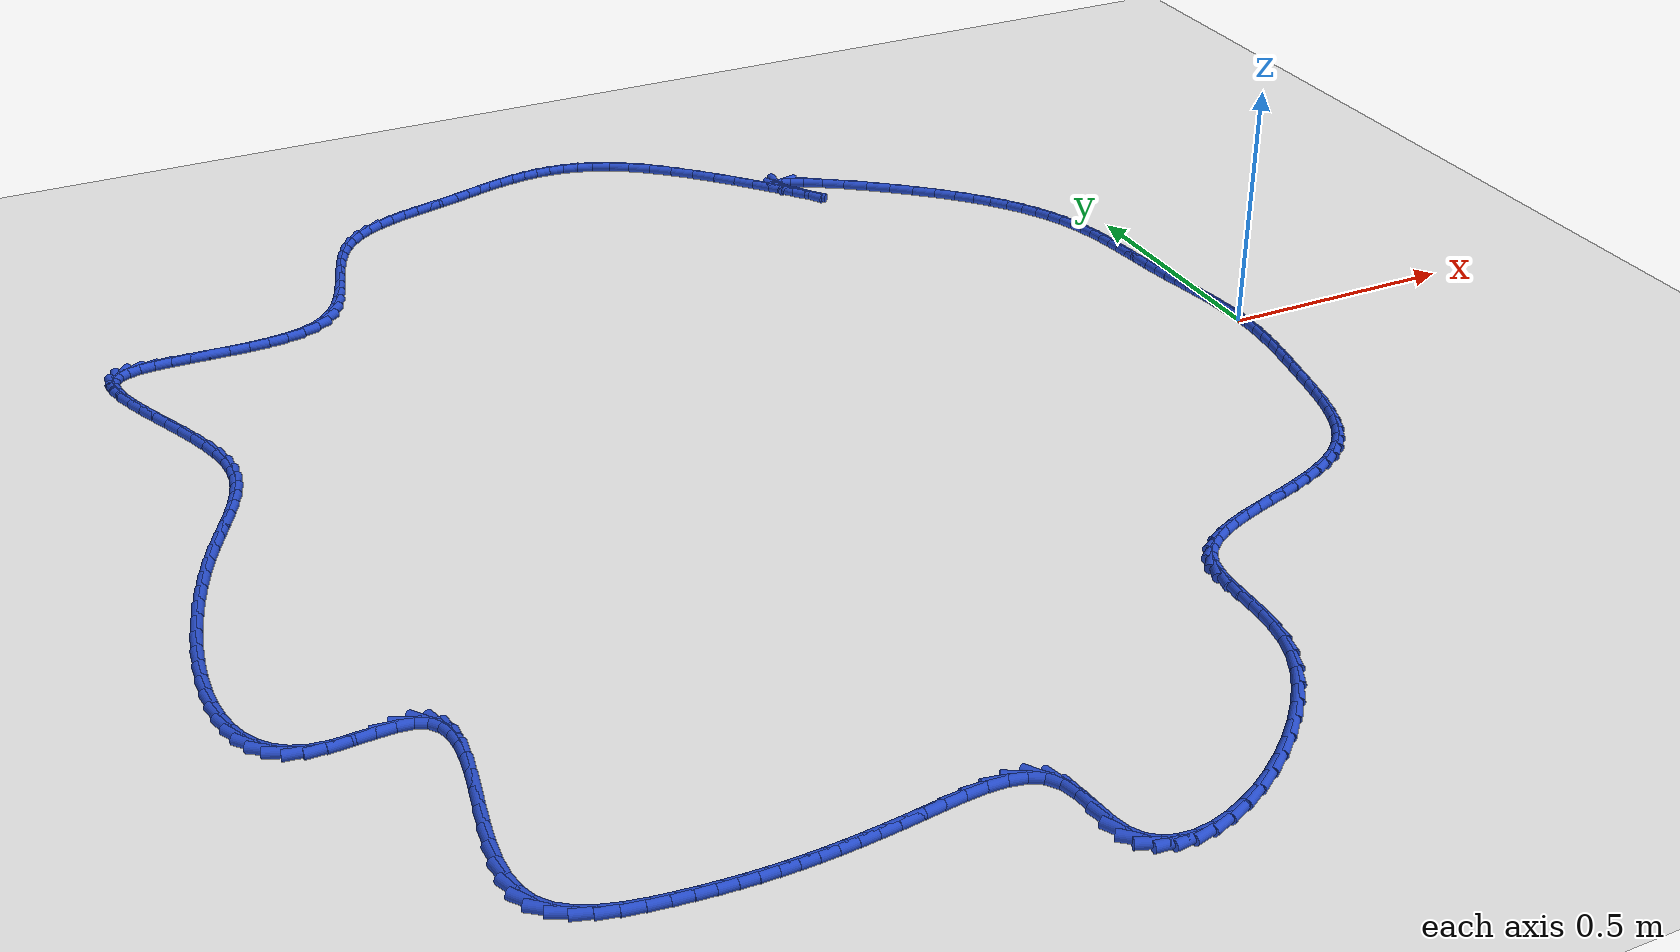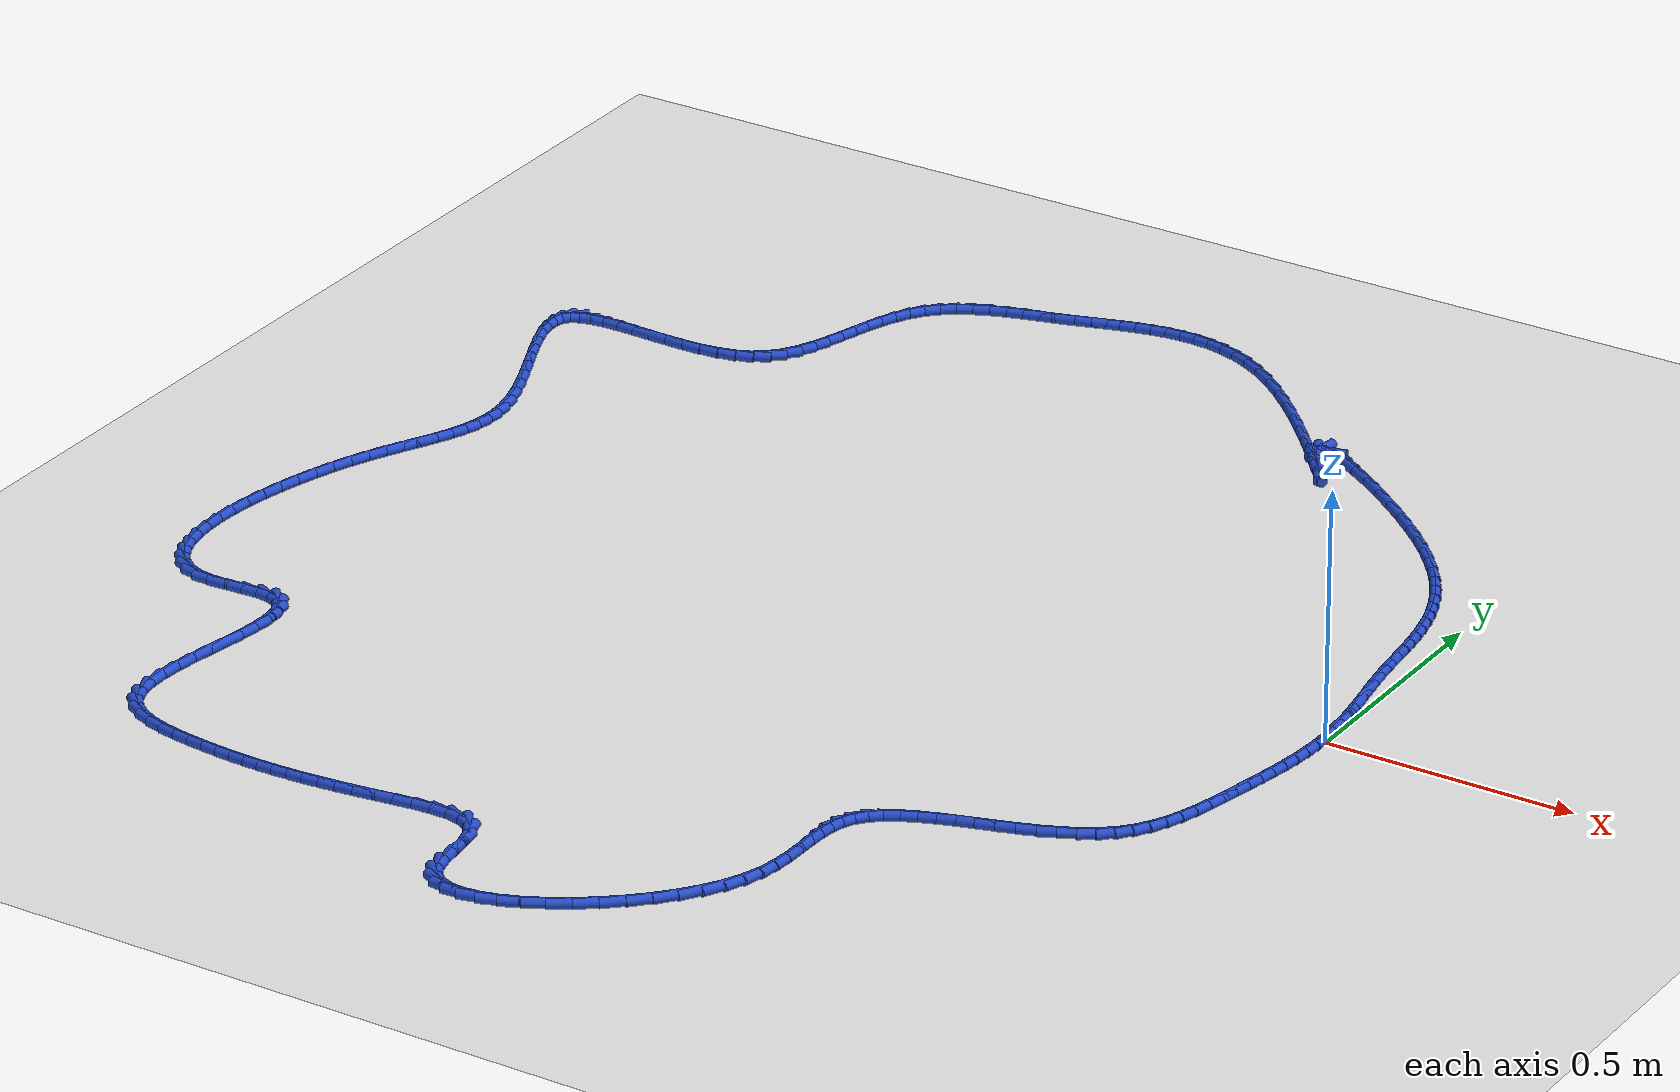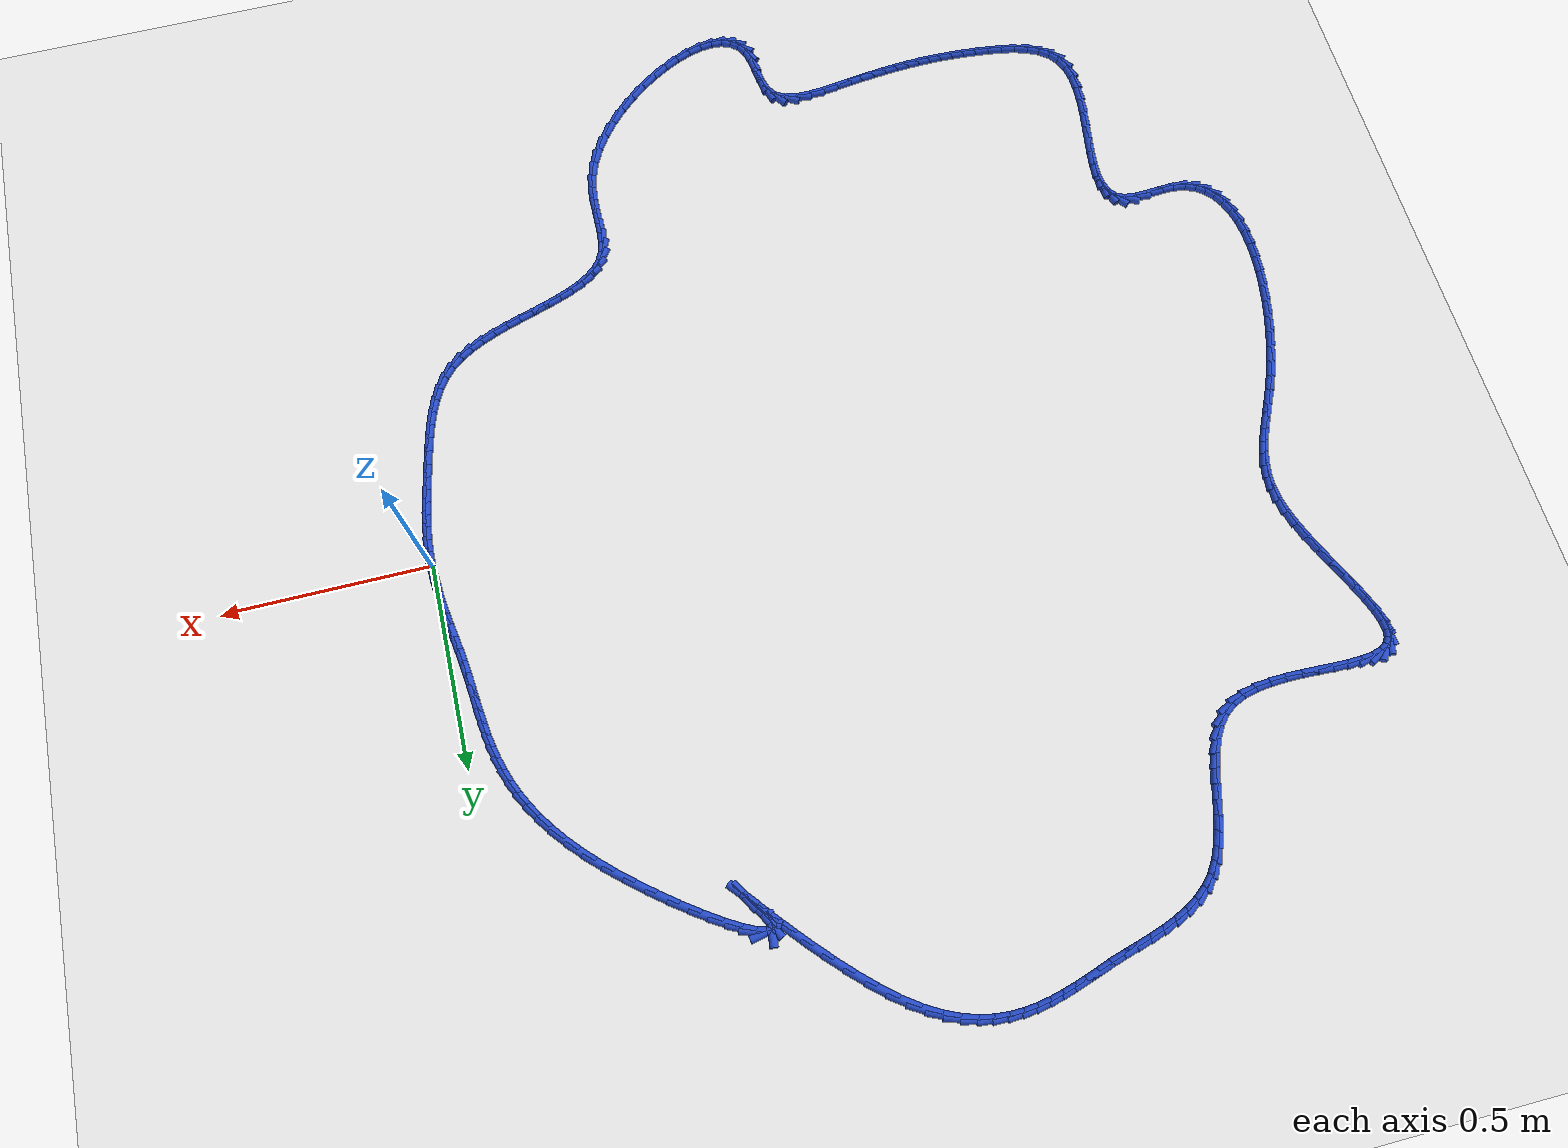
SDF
<sdf version="1.6">
 <world name="default">
  <light name="sun" type="directional">
   <pose>0 0 10 0 -0 0</pose>
   <diffuse>0.8 0.8 0.8 1</diffuse>
   <specular>0.2 0.2 0.2 1</specular>
   <attenuation>
    <range>1000</range>
    <constant>0.9</constant>
    <linear>0.01</linear>
    <quadratic>0.001</quadratic>
   </attenuation>
   <direction>-0.5 0.1 -0.9</direction>
  </light>
  <model name="ground_plane">
   <static>1</static>
   <link name="link">
    <collision name="collision">
     <geometry><plane><normal>0 0 1</normal><size>100 100</size></plane></geometry>
     <surface><friction><ode><mu>100</mu><mu2>50</mu2></ode></friction></surface>
    </collision>
    <visual name="visual">
     <cast_shadows>0</cast_shadows>
     <geometry><plane><normal>0 0 1</normal><size>100 100</size></plane></geometry>
     <material>
      <script><uri>file://media/materials/scripts/gazebo.material</uri><name>Gazebo/WhiteGlow</name></script>
     </material>
    </visual>
   </link>
  </model>
  <gravity>0 0 -9.8</gravity>
  <magnetic_field>6e-06 2.3e-05 -4.2e-05</magnetic_field>
  <atmosphere type="adiabatic"/>
  <physics name="default_physics" default="0" type="ode">
   <max_step_size>0.001</max_step_size>
   <real_time_factor>1</real_time_factor>
   <real_time_update_rate>1000</real_time_update_rate>
  </physics>
  <scene><ambient>0.4 0.4 0.4 1</ambient><background>0.7 0.7 0.7 1</background><shadows>1</shadows></scene>
  <spherical_coordinates>
   <surface_model>EARTH_WGS84</surface_model>
   <latitude_deg>0</latitude_deg>
   <longitude_deg>0</longitude_deg>
   <elevation>0</elevation>
   <heading_deg>0</heading_deg>
  </spherical_coordinates>
  <model name="line">
   <link name="link_0">
    <pose>0.0 6.938893903907228e-18 0.01 0 1.57 -1.5258611969889966</pose>
    <collision name="collision">
     <geometry><cylinder><radius>0.01</radius><length>0.08</length></cylinder></geometry>
    </collision>
    <visual name="visual">
     <material>
      <script><name>Gazebo/Blue</name><uri>file://media/materials/scripts/gazebo.material</uri></script>
     </material>
     <geometry><cylinder><radius>0.01</radius><length>0.08</length></cylinder></geometry>
    </visual>
   </link>
   <link name="link_1">
    <pose>-0.0014691972529593657 0.03267395187623161 0.01 0 1.57 -1.4818103259888868</pose>
    <collision name="collision">
     <geometry><cylinder><radius>0.01</radius><length>0.08</length></cylinder></geometry>
    </collision>
    <visual name="visual">
     <material>
      <script><name>Gazebo/Blue</name><uri>file://media/materials/scripts/gazebo.material</uri></script>
     </material>
     <geometry><cylinder><radius>0.01</radius><length>0.08</length></cylinder></geometry>
    </visual>
   </link>
   <link name="link_2">
    <pose>-0.004399185523161368 0.06551339230322885 0.01 0 1.57 -1.4479531760077484</pose>
    <collision name="collision">
     <geometry><cylinder><radius>0.01</radius><length>0.08</length></cylinder></geometry>
    </collision>
    <visual name="visual">
     <material>
      <script><name>Gazebo/Blue</name><uri>file://media/materials/scripts/gazebo.material</uri></script>
     </material>
     <geometry><cylinder><radius>0.01</radius><length>0.08</length></cylinder></geometry>
    </visual>
   </link>
   <link name="link_3">
    <pose>-0.00845889065402072 0.09839486448585638 0.01 0 1.57 -1.4237453703894456</pose>
    <collision name="collision">
     <geometry><cylinder><radius>0.01</radius><length>0.08</length></cylinder></geometry>
    </collision>
    <visual name="visual">
     <material>
      <script><name>Gazebo/Blue</name><uri>file://media/materials/scripts/gazebo.material</uri></script>
     </material>
     <geometry><cylinder><radius>0.01</radius><length>0.08</length></cylinder></geometry>
    </visual>
   </link>
   <link name="link_4">
    <pose>-0.013317238488952145 0.1311949116289788 0.01 0 1.57 -1.4088316946596</pose>
    <collision name="collision">
     <geometry><cylinder><radius>0.01</radius><length>0.08</length></cylinder></geometry>
    </collision>
    <visual name="visual">
     <material>
      <script><name>Gazebo/Blue</name><uri>file://media/materials/scripts/gazebo.material</uri></script>
     </material>
     <geometry><cylinder><radius>0.01</radius><length>0.08</length></cylinder></geometry>
    </visual>
   </link>
   <link name="link_5">
    <pose>-0.01864315487137037 0.16379007693746078 0.01 0 1.57 -1.40309752246018</pose>
    <collision name="collision">
     <geometry><cylinder><radius>0.01</radius><length>0.08</length></cylinder></geometry>
    </collision>
    <visual name="visual">
     <material>
      <script><name>Gazebo/Blue</name><uri>file://media/materials/scripts/gazebo.material</uri></script>
     </material>
     <geometry><cylinder><radius>0.01</radius><length>0.08</length></cylinder></geometry>
    </visual>
   </link>
   <link name="link_6">
    <pose>-0.024105565644690127 0.19605690361616698 0.01 0 1.57 -1.4067082490515426</pose>
    <collision name="collision">
     <geometry><cylinder><radius>0.01</radius><length>0.08</length></cylinder></geometry>
    </collision>
    <visual name="visual">
     <material>
      <script><name>Gazebo/Blue</name><uri>file://media/materials/scripts/gazebo.material</uri></script>
     </material>
     <geometry><cylinder><radius>0.01</radius><length>0.08</length></cylinder></geometry>
    </visual>
   </link>
   <link name="link_7">
    <pose>-0.029373396652326127 0.2278719348699619 0.01 0 1.57 -1.4201471205385507</pose>
    <collision name="collision">
     <geometry><cylinder><radius>0.01</radius><length>0.08</length></cylinder></geometry>
    </collision>
    <visual name="visual">
     <material>
      <script><name>Gazebo/Blue</name><uri>file://media/materials/scripts/gazebo.material</uri></script>
     </material>
     <geometry><cylinder><radius>0.01</radius><length>0.08</length></cylinder></geometry>
    </visual>
   </link>
   <link name="link_8">
    <pose>-0.03411557382917909 0.2591117139365208 0.01 0 1.57 -1.4408508744497242</pose>
    <collision name="collision">
     <geometry><cylinder><radius>0.01</radius><length>0.08</length></cylinder></geometry>
    </collision>
    <visual name="visual">
     <material>
      <script><name>Gazebo/Blue</name><uri>file://media/materials/scripts/gazebo.material</uri></script>
     </material>
     <geometry><cylinder><radius>0.01</radius><length>0.08</length></cylinder></geometry>
    </visual>
   </link>
   <link name="link_9">
    <pose>-0.03811193521220985 0.28969256152682127 0.01 0 1.57 -1.4558903674333454</pose>
    <collision name="collision">
     <geometry><cylinder><radius>0.01</radius><length>0.08</length></cylinder></geometry>
    </collision>
    <visual name="visual">
     <material>
      <script><name>Gazebo/Blue</name><uri>file://media/materials/scripts/gazebo.material</uri></script>
     </material>
     <geometry><cylinder><radius>0.01</radius><length>0.08</length></cylinder></geometry>
    </visual>
   </link>
   <link name="link_10">
    <pose>-0.041573545635154155 0.3196854533631289 0.01 0 1.57 -1.4613630848294605</pose>
    <collision name="collision">
     <geometry><cylinder><radius>0.01</radius><length>0.08</length></cylinder></geometry>
    </collision>
    <visual name="visual">
     <material>
      <script><name>Gazebo/Blue</name><uri>file://media/materials/scripts/gazebo.material</uri></script>
     </material>
     <geometry><cylinder><radius>0.01</radius><length>0.08</length></cylinder></geometry>
    </visual>
   </link>
   <link name="link_11">
    <pose>-0.04481625769705502 0.34919894621125214 0.01 0 1.57 -1.4566968560215747</pose>
    <collision name="collision">
     <geometry><cylinder><radius>0.01</radius><length>0.08</length></cylinder></geometry>
    </collision>
    <visual name="visual">
     <material>
      <script><name>Gazebo/Blue</name><uri>file://media/materials/scripts/gazebo.material</uri></script>
     </material>
     <geometry><cylinder><radius>0.01</radius><length>0.08</length></cylinder></geometry>
    </visual>
   </link>
   <link name="link_12">
    <pose>-0.04815592399695554 0.37834159683699936 0.01 0 1.57 -1.441588549745439</pose>
    <collision name="collision">
     <geometry><cylinder><radius>0.01</radius><length>0.08</length></cylinder></geometry>
    </collision>
    <visual name="visual">
     <material>
      <script><name>Gazebo/Blue</name><uri>file://media/materials/scripts/gazebo.material</uri></script>
     </material>
     <geometry><cylinder><radius>0.01</radius><length>0.08</length></cylinder></geometry>
    </visual>
   </link>
   <link name="link_13">
    <pose>-0.05190839713389876 0.4072219620061788 0.01 0 1.57 -1.4160512049310834</pose>
    <collision name="collision">
     <geometry><cylinder><radius>0.01</radius><length>0.08</length></cylinder></geometry>
    </collision>
    <visual name="visual">
     <material>
      <script><name>Gazebo/Blue</name><uri>file://media/materials/scripts/gazebo.material</uri></script>
     </material>
     <geometry><cylinder><radius>0.01</radius><length>0.08</length></cylinder></geometry>
    </visual>
   </link>
   <link name="link_14">
    <pose>-0.056389529706927774 0.435948598484599 0.01 0 1.57 -1.3804725655771617</pose>
    <collision name="collision">
     <geometry><cylinder><radius>0.01</radius><length>0.08</length></cylinder></geometry>
    </collision>
    <visual name="visual">
     <material>
      <script><name>Gazebo/Blue</name><uri>file://media/materials/scripts/gazebo.material</uri></script>
     </material>
     <geometry><cylinder><radius>0.01</radius><length>0.08</length></cylinder></geometry>
    </visual>
   </link>
   <link name="link_15">
    <pose>-0.06191517431508562 0.4646300630380682 0.01 0 1.57 -1.3356709402866982</pose>
    <collision name="collision">
     <geometry><cylinder><radius>0.01</radius><length>0.08</length></cylinder></geometry>
    </collision>
    <visual name="visual">
     <material>
      <script><name>Gazebo/Blue</name><uri>file://media/materials/scripts/gazebo.material</uri></script>
     </material>
     <geometry><cylinder><radius>0.01</radius><length>0.08</length></cylinder></geometry>
    </visual>
   </link>
   <link name="link_16">
    <pose>-0.0688011835574154 0.49337491243239495 0.01 0 1.57 -1.2829224669733459</pose>
    <collision name="collision">
     <geometry><cylinder><radius>0.01</radius><length>0.08</length></cylinder></geometry>
    </collision>
    <visual name="visual">
     <material>
      <script><name>Gazebo/Blue</name><uri>file://media/materials/scripts/gazebo.material</uri></script>
     </material>
     <geometry><cylinder><radius>0.01</radius><length>0.08</length></cylinder></geometry>
    </visual>
   </link>
   <link name="link_17">
    <pose>-0.07736341003296011 0.5222917034333874 0.01 0 1.57 -1.2239293444627077</pose>
    <collision name="collision">
     <geometry><cylinder><radius>0.01</radius><length>0.08</length></cylinder></geometry>
    </collision>
    <visual name="visual">
     <material>
      <script><name>Gazebo/Blue</name><uri>file://media/materials/scripts/gazebo.material</uri></script>
     </material>
     <geometry><cylinder><radius>0.01</radius><length>0.08</length></cylinder></geometry>
    </visual>
   </link>
   <link name="link_18">
    <pose>-0.08791770634076287 0.551488992806854 0.01 0 1.57 -1.1607090477947983</pose>
    <collision name="collision">
     <geometry><cylinder><radius>0.01</radius><length>0.08</length></cylinder></geometry>
    </collision>
    <visual name="visual">
     <material>
      <script><name>Gazebo/Blue</name><uri>file://media/materials/scripts/gazebo.material</uri></script>
     </material>
     <geometry><cylinder><radius>0.01</radius><length>0.08</length></cylinder></geometry>
    </visual>
   </link>
   <link name="link_19">
    <pose>-0.10077992507986677 0.5810753373186034 0.01 0 1.57 -1.0954111832593871</pose>
    <collision name="collision">
     <geometry><cylinder><radius>0.01</radius><length>0.08</length></cylinder></geometry>
    </collision>
    <visual name="visual">
     <material>
      <script><name>Gazebo/Blue</name><uri>file://media/materials/scripts/gazebo.material</uri></script>
     </material>
     <geometry><cylinder><radius>0.01</radius><length>0.08</length></cylinder></geometry>
    </visual>
   </link>
   <link name="link_20">
    <pose>-0.11626591884931481 0.6111592937344434 0.01 0 1.57 -1.0301002374866681</pose>
    <collision name="collision">
     <geometry><cylinder><radius>0.01</radius><length>0.08</length></cylinder></geometry>
    </collision>
    <visual name="visual">
     <material>
      <script><name>Gazebo/Blue</name><uri>file://media/materials/scripts/gazebo.material</uri></script>
     </material>
     <geometry><cylinder><radius>0.01</radius><length>0.08</length></cylinder></geometry>
    </visual>
   </link>
   <link name="link_21">
    <pose>-0.1346915402481501 0.6418494188201831 0.01 0 1.57 -0.9665598207683193</pose>
    <collision name="collision">
     <geometry><cylinder><radius>0.01</radius><length>0.08</length></cylinder></geometry>
    </collision>
    <visual name="visual">
     <material>
      <script><name>Gazebo/Blue</name><uri>file://media/materials/scripts/gazebo.material</uri></script>
     </material>
     <geometry><cylinder><radius>0.01</radius><length>0.08</length></cylinder></geometry>
    </visual>
   </link>
   <link name="link_22">
    <pose>-0.15637264187541572 0.6732542693416305 0.01 0 1.57 -0.9061651090211164</pose>
    <collision name="collision">
     <geometry><cylinder><radius>0.01</radius><length>0.08</length></cylinder></geometry>
    </collision>
    <visual name="visual">
     <material>
      <script><name>Gazebo/Blue</name><uri>file://media/materials/scripts/gazebo.material</uri></script>
     </material>
     <geometry><cylinder><radius>0.01</radius><length>0.08</length></cylinder></geometry>
    </visual>
   </link>
   <link name="link_23">
    <pose>-0.18162507633015473 0.705482402064594 0.01 0 1.57 -0.8498413605181512</pose>
    <collision name="collision">
     <geometry><cylinder><radius>0.01</radius><length>0.08</length></cylinder></geometry>
    </collision>
    <visual name="visual">
     <material>
      <script><name>Gazebo/Blue</name><uri>file://media/materials/scripts/gazebo.material</uri></script>
     </material>
     <geometry><cylinder><radius>0.01</radius><length>0.08</length></cylinder></geometry>
    </visual>
   </link>
   <link name="link_24">
    <pose>-0.2107646962114102 0.7386423737548817 0.01 0 1.57 -0.7980961942140037</pose>
    <collision name="collision">
     <geometry><cylinder><radius>0.01</radius><length>0.08</length></cylinder></geometry>
    </collision>
    <visual name="visual">
     <material>
      <script><name>Gazebo/Blue</name><uri>file://media/materials/scripts/gazebo.material</uri></script>
     </material>
     <geometry><cylinder><radius>0.01</radius><length>0.08</length></cylinder></geometry>
    </visual>
   </link>
   <link name="link_25">
    <pose>-0.2441073541182251 0.7728427411783025 0.01 0 1.57 -0.7521877125468822</pose>
    <collision name="collision">
     <geometry><cylinder><radius>0.01</radius><length>0.08</length></cylinder></geometry>
    </collision>
    <visual name="visual">
     <material>
      <script><name>Gazebo/Blue</name><uri>file://media/materials/scripts/gazebo.material</uri></script>
     </material>
     <geometry><cylinder><radius>0.01</radius><length>0.08</length></cylinder></geometry>
    </visual>
   </link>
   <link name="link_26">
    <pose>-0.281695706073974 0.8080138305256461 0.01 0 1.57 -0.7146133789067807</pose>
    <collision name="collision">
     <geometry><cylinder><radius>0.01</radius><length>0.08</length></cylinder></geometry>
    </collision>
    <visual name="visual">
     <material>
      <script><name>Gazebo/Blue</name><uri>file://media/materials/scripts/gazebo.material</uri></script>
     </material>
     <geometry><cylinder><radius>0.01</radius><length>0.08</length></cylinder></geometry>
    </visual>
   </link>
   <link name="link_27">
    <pose>-0.3223672091477742 0.8432997088550509 0.01 0 1.57 -0.6822002102609821</pose>
    <collision name="collision">
     <geometry><cylinder><radius>0.01</radius><length>0.08</length></cylinder></geometry>
    </collision>
    <visual name="visual">
     <material>
      <script><name>Gazebo/Blue</name><uri>file://media/materials/scripts/gazebo.material</uri></script>
     </material>
     <geometry><cylinder><radius>0.01</radius><length>0.08</length></cylinder></geometry>
    </visual>
   </link>
   <link name="link_28">
    <pose>-0.3646270855249644 0.8776276966778425 0.01 0 1.57 -0.651496474279758</pose>
    <collision name="collision">
     <geometry><cylinder><radius>0.01</radius><length>0.08</length></cylinder></geometry>
    </collision>
    <visual name="visual">
     <material>
      <script><name>Gazebo/Blue</name><uri>file://media/materials/scripts/gazebo.material</uri></script>
     </material>
     <geometry><cylinder><radius>0.01</radius><length>0.08</length></cylinder></geometry>
    </visual>
   </link>
   <link name="link_29">
    <pose>-0.4069805469184418 0.9099251076732369 0.01 0 1.57 -0.619319708851095</pose>
    <collision name="collision">
     <geometry><cylinder><radius>0.01</radius><length>0.08</length></cylinder></geometry>
    </collision>
    <visual name="visual">
     <material>
      <script><name>Gazebo/Blue</name><uri>file://media/materials/scripts/gazebo.material</uri></script>
     </material>
     <geometry><cylinder><radius>0.01</radius><length>0.08</length></cylinder></geometry>
    </visual>
   </link>
   <link name="link_30">
    <pose>-0.4479328050411033 0.939119255520449 0.01 0 1.57 -0.5815599124522028</pose>
    <collision name="collision">
     <geometry><cylinder><radius>0.01</radius><length>0.08</length></cylinder></geometry>
    </collision>
    <visual name="visual">
     <material>
      <script><name>Gazebo/Blue</name><uri>file://media/materials/scripts/gazebo.material</uri></script>
     </material>
     <geometry><cylinder><radius>0.01</radius><length>0.08</length></cylinder></geometry>
    </visual>
   </link>
   <link name="link_31">
    <pose>-0.4859890716058458 0.9641374538986937 0.01 0 1.57 -0.530980825086728</pose>
    <collision name="collision">
     <geometry><cylinder><radius>0.01</radius><length>0.08</length></cylinder></geometry>
    </collision>
    <visual name="visual">
     <material>
      <script><name>Gazebo/Blue</name><uri>file://media/materials/scripts/gazebo.material</uri></script>
     </material>
     <geometry><cylinder><radius>0.01</radius><length>0.08</length></cylinder></geometry>
    </visual>
   </link>
   <link name="link_32">
    <pose>-0.5196545583255666 0.9839070164871867 0.01 0 1.57 -0.4508463630549518</pose>
    <collision name="collision">
     <geometry><cylinder><radius>0.01</radius><length>0.08</length></cylinder></geometry>
    </collision>
    <visual name="visual">
     <material>
      <script><name>Gazebo/Blue</name><uri>file://media/materials/scripts/gazebo.material</uri></script>
     </material>
     <geometry><cylinder><radius>0.01</radius><length>0.08</length></cylinder></geometry>
    </visual>
   </link>
   <link name="link_33">
    <pose>-0.5474344769131626 0.9973552569651433 0.01 0 1.57 -0.2885023062760594</pose>
    <collision name="collision">
     <geometry><cylinder><radius>0.01</radius><length>0.08</length></cylinder></geometry>
    </collision>
    <visual name="visual">
     <material>
      <script><name>Gazebo/Blue</name><uri>file://media/materials/scripts/gazebo.material</uri></script>
     </material>
     <geometry><cylinder><radius>0.01</radius><length>0.08</length></cylinder></geometry>
    </visual>
   </link>
   <link name="link_34">
    <pose>-0.5678340390815307 1.0034094890117786 0.01 0 1.57 0.2063550951875672</pose>
    <collision name="collision">
     <geometry><cylinder><radius>0.01</radius><length>0.08</length></cylinder></geometry>
    </collision>
    <visual name="visual">
     <material>
      <script><name>Gazebo/Blue</name><uri>file://media/materials/scripts/gazebo.material</uri></script>
     </material>
     <geometry><cylinder><radius>0.01</radius><length>0.08</length></cylinder></geometry>
    </visual>
   </link>
   <link name="link_35">
    <pose>-0.5793584565435682 1.0009970263063077 0.01 0 1.57 1.4745004073202177</pose>
    <collision name="collision">
     <geometry><cylinder><radius>0.01</radius><length>0.08</length></cylinder></geometry>
    </collision>
    <visual name="visual">
     <material>
      <script><name>Gazebo/Blue</name><uri>file://media/materials/scripts/gazebo.material</uri></script>
     </material>
     <geometry><cylinder><radius>0.01</radius><length>0.08</length></cylinder></geometry>
    </visual>
   </link>
   <link name="link_36">
    <pose>-0.5805129410121718 0.989045182527946 0.01 0 1.57 -1.1282633665600263</pose>
    <collision name="collision">
     <geometry><cylinder><radius>0.01</radius><length>0.08</length></cylinder></geometry>
    </collision>
    <visual name="visual">
     <material>
      <script><name>Gazebo/Blue</name><uri>file://media/materials/scripts/gazebo.material</uri></script>
     </material>
     <geometry><cylinder><radius>0.01</radius><length>0.08</length></cylinder></geometry>
    </visual>
   </link>
   <link name="link_37">
    <pose>-0.5698392278463899 0.9665210304962868 0.01 0 1.57 -0.9907821835656347</pose>
    <collision name="collision">
     <geometry><cylinder><radius>0.01</radius><length>0.08</length></cylinder></geometry>
    </collision>
    <visual name="visual">
     <material>
      <script><name>Gazebo/Blue</name><uri>file://media/materials/scripts/gazebo.material</uri></script>
     </material>
     <geometry><cylinder><radius>0.01</radius><length>0.08</length></cylinder></geometry>
    </visual>
   </link>
   <link name="link_38">
    <pose>-0.551454894785037 0.9384614285880154 0.01 0 1.57 -0.9747282628831557</pose>
    <collision name="collision">
     <geometry><cylinder><radius>0.01</radius><length>0.08</length></cylinder></geometry>
    </collision>
    <visual name="visual">
     <material>
      <script><name>Gazebo/Blue</name><uri>file://media/materials/scripts/gazebo.material</uri></script>
     </material>
     <geometry><cylinder><radius>0.01</radius><length>0.08</length></cylinder></geometry>
    </visual>
   </link>
   <link name="link_39">
    <pose>-0.5390990317790039 0.9202476504994181 0.01 0 1.57 -1.0492456244938666</pose>
    <collision name="collision">
     <geometry><cylinder><radius>0.01</radius><length>0.08</length></cylinder></geometry>
    </collision>
    <visual name="visual">
     <material>
      <script><name>Gazebo/Blue</name><uri>file://media/materials/scripts/gazebo.material</uri></script>
     </material>
     <geometry><cylinder><radius>0.01</radius><length>0.08</length></cylinder></geometry>
    </visual>
   </link>
   <link name="link_40">
    <pose>-0.5362549353686903 0.9152981483639404 0.01 0 1.57 -0.857212973098952</pose>
    <collision name="collision">
     <geometry><cylinder><radius>0.01</radius><length>0.08</length></cylinder></geometry>
    </collision>
    <visual name="visual">
     <material>
      <script><name>Gazebo/Blue</name><uri>file://media/materials/scripts/gazebo.material</uri></script>
     </material>
     <geometry><cylinder><radius>0.01</radius><length>0.08</length></cylinder></geometry>
    </visual>
   </link>
   <link name="link_41">
    <pose>-0.5419561016126783 0.9218831644203921 0.01 0 1.57 -0.8898527232242053</pose>
    <collision name="collision">
     <geometry><cylinder><radius>0.01</radius><length>0.08</length></cylinder></geometry>
    </collision>
    <visual name="visual">
     <material>
      <script><name>Gazebo/Blue</name><uri>file://media/materials/scripts/gazebo.material</uri></script>
     </material>
     <geometry><cylinder><radius>0.01</radius><length>0.08</length></cylinder></geometry>
    </visual>
   </link>
   <link name="link_42">
    <pose>-0.5552272835385784 0.9382628256319117 0.01 0 1.57 -0.8881600334387298</pose>
    <collision name="collision">
     <geometry><cylinder><radius>0.01</radius><length>0.08</length></cylinder></geometry>
    </collision>
    <visual name="visual">
     <material>
      <script><name>Gazebo/Blue</name><uri>file://media/materials/scripts/gazebo.material</uri></script>
     </material>
     <geometry><cylinder><radius>0.01</radius><length>0.08</length></cylinder></geometry>
    </visual>
   </link>
   <link name="link_43">
    <pose>-0.5750932341740017 0.9626972589616377 0.01 0 1.57 -0.8787312259694798</pose>
    <collision name="collision">
     <geometry><cylinder><radius>0.01</radius><length>0.08</length></cylinder></geometry>
    </collision>
    <visual name="visual">
     <material>
      <script><name>Gazebo/Blue</name><uri>file://media/materials/scripts/gazebo.material</uri></script>
     </material>
     <geometry><cylinder><radius>0.01</radius><length>0.08</length></cylinder></geometry>
    </visual>
   </link>
   <link name="link_44">
    <pose>-0.6005787065465583 0.9934465913727076 0.01 0 1.57 -0.8645948208912567</pose>
    <collision name="collision">
     <geometry><cylinder><radius>0.01</radius><length>0.08</length></cylinder></geometry>
    </collision>
    <visual name="visual">
     <material>
      <script><name>Gazebo/Blue</name><uri>file://media/materials/scripts/gazebo.material</uri></script>
     </material>
     <geometry><cylinder><radius>0.01</radius><length>0.08</length></cylinder></geometry>
    </visual>
   </link>
   <link name="link_45">
    <pose>-0.6307084536838592 1.0287709498282607 0.01 0 1.57 -0.8459250361362335</pose>
    <collision name="collision">
     <geometry><cylinder><radius>0.01</radius><length>0.08</length></cylinder></geometry>
    </collision>
    <visual name="visual">
     <material>
      <script><name>Gazebo/Blue</name><uri>file://media/materials/scripts/gazebo.material</uri></script>
     </material>
     <geometry><cylinder><radius>0.01</radius><length>0.08</length></cylinder></geometry>
    </visual>
   </link>
   <link name="link_46">
    <pose>-0.6645072286135147 1.0669304612914339 0.01 0 1.57 -0.821848446545115</pose>
    <collision name="collision">
     <geometry><cylinder><radius>0.01</radius><length>0.08</length></cylinder></geometry>
    </collision>
    <visual name="visual">
     <material>
      <script><name>Gazebo/Blue</name><uri>file://media/materials/scripts/gazebo.material</uri></script>
     </material>
     <geometry><cylinder><radius>0.01</radius><length>0.08</length></cylinder></geometry>
    </visual>
   </link>
   <link name="link_47">
    <pose>-0.7009997843631356 1.1061852527253668 0.01 0 1.57 -0.790593405373712</pose>
    <collision name="collision">
     <geometry><cylinder><radius>0.01</radius><length>0.08</length></cylinder></geometry>
    </collision>
    <visual name="visual">
     <material>
      <script><name>Gazebo/Blue</name><uri>file://media/materials/scripts/gazebo.material</uri></script>
     </material>
     <geometry><cylinder><radius>0.01</radius><length>0.08</length></cylinder></geometry>
    </visual>
   </link>
   <link name="link_48">
    <pose>-0.7392108739603325 1.144795451093197 0.01 0 1.57 -0.7491193252465159</pose>
    <collision name="collision">
     <geometry><cylinder><radius>0.01</radius><length>0.08</length></cylinder></geometry>
    </collision>
    <visual name="visual">
     <material>
      <script><name>Gazebo/Blue</name><uri>file://media/materials/scripts/gazebo.material</uri></script>
     </material>
     <geometry><cylinder><radius>0.01</radius><length>0.08</length></cylinder></geometry>
    </visual>
   </link>
   <link name="link_49">
    <pose>-0.7781652504327157 1.1810211833580624 0.01 0 1.57 -0.6921832481922636</pose>
    <collision name="collision">
     <geometry><cylinder><radius>0.01</radius><length>0.08</length></cylinder></geometry>
    </collision>
    <visual name="visual">
     <material>
      <script><name>Gazebo/Blue</name><uri>file://media/materials/scripts/gazebo.material</uri></script>
     </material>
     <geometry><cylinder><radius>0.01</radius><length>0.08</length></cylinder></geometry>
    </visual>
   </link>
   <link name="link_50">
    <pose>-0.8168876668078962 1.2131225764831015 0.01 0 1.57 -0.6135892848076143</pose>
    <collision name="collision">
     <geometry><cylinder><radius>0.01</radius><length>0.08</length></cylinder></geometry>
    </collision>
    <visual name="visual">
     <material>
      <script><name>Gazebo/Blue</name><uri>file://media/materials/scripts/gazebo.material</uri></script>
     </material>
     <geometry><cylinder><radius>0.01</radius><length>0.08</length></cylinder></geometry>
    </visual>
   </link>
   <link name="link_51">
    <pose>-0.8545412952096035 1.239641082893837 0.01 0 1.57 -0.5211288251336482</pose>
    <collision name="collision">
     <geometry><cylinder><radius>0.01</radius><length>0.08</length></cylinder></geometry>
    </collision>
    <visual name="visual">
     <material>
      <script><name>Gazebo/Blue</name><uri>file://media/materials/scripts/gazebo.material</uri></script>
     </material>
     <geometry><cylinder><radius>0.01</radius><length>0.08</length></cylinder></geometry>
    </visual>
   </link>
   <link name="link_52">
    <pose>-0.8910055196930917 1.26057379703665 0.01 0 1.57 -0.4202678960532829</pose>
    <collision name="collision">
     <geometry><cylinder><radius>0.01</radius><length>0.08</length></cylinder></geometry>
    </collision>
    <visual name="visual">
     <material>
      <script><name>Gazebo/Blue</name><uri>file://media/materials/scripts/gazebo.material</uri></script>
     </material>
     <geometry><cylinder><radius>0.01</radius><length>0.08</length></cylinder></geometry>
    </visual>
   </link>
   <link name="link_53">
    <pose>-0.9263906785535868 1.2763872089122297 0.01 0 1.57 -0.3135866445528265</pose>
    <collision name="collision">
     <geometry><cylinder><radius>0.01</radius><length>0.08</length></cylinder></geometry>
    </collision>
    <visual name="visual">
     <material>
      <script><name>Gazebo/Blue</name><uri>file://media/materials/scripts/gazebo.material</uri></script>
     </material>
     <geometry><cylinder><radius>0.01</radius><length>0.08</length></cylinder></geometry>
    </visual>
   </link>
   <link name="link_54">
    <pose>-0.9608072229423574 1.2875480378919182 0.01 0 1.57 -0.20492800180479723</pose>
    <collision name="collision">
     <geometry><cylinder><radius>0.01</radius><length>0.08</length></cylinder></geometry>
    </collision>
    <visual name="visual">
     <material>
      <script><name>Gazebo/Blue</name><uri>file://media/materials/scripts/gazebo.material</uri></script>
     </material>
     <geometry><cylinder><radius>0.01</radius><length>0.08</length></cylinder></geometry>
    </visual>
   </link>
   <link name="link_55">
    <pose>-0.994365604010672 1.2945230033470574 0.01 0 1.57 -0.09890678045338026</pose>
    <collision name="collision">
     <geometry><cylinder><radius>0.01</radius><length>0.08</length></cylinder></geometry>
    </collision>
    <visual name="visual">
     <material>
      <script><name>Gazebo/Blue</name><uri>file://media/materials/scripts/gazebo.material</uri></script>
     </material>
     <geometry><cylinder><radius>0.01</radius><length>0.08</length></cylinder></geometry>
    </visual>
   </link>
   <link name="link_56">
    <pose>-1.0271762729097997 1.2977788246489894 0.01 0 1.57 -0.0001055691727228564</pose>
    <collision name="collision">
     <geometry><cylinder><radius>0.01</radius><length>0.08</length></cylinder></geometry>
    </collision>
    <visual name="visual">
     <material>
      <script><name>Gazebo/Blue</name><uri>file://media/materials/scripts/gazebo.material</uri></script>
     </material>
     <geometry><cylinder><radius>0.01</radius><length>0.08</length></cylinder></geometry>
    </visual>
   </link>
   <link name="link_57">
    <pose>-1.059349680791009 1.2977822211690557 0.01 0 1.57 0.08769262491750153</pose>
    <collision name="collision">
     <geometry><cylinder><radius>0.01</radius><length>0.08</length></cylinder></geometry>
    </collision>
    <visual name="visual">
     <material>
      <script><name>Gazebo/Blue</name><uri>file://media/materials/scripts/gazebo.material</uri></script>
     </material>
     <geometry><cylinder><radius>0.01</radius><length>0.08</length></cylinder></geometry>
    </visual>
   </link>
   <link name="link_58">
    <pose>-1.0909962788055687 1.2949999122785985 0.01 0 1.57 0.16191478963123873</pose>
    <collision name="collision">
     <geometry><cylinder><radius>0.01</radius><length>0.08</length></cylinder></geometry>
    </collision>
    <visual name="visual">
     <material>
      <script><name>Gazebo/Blue</name><uri>file://media/materials/scripts/gazebo.material</uri></script>
     </material>
     <geometry><cylinder><radius>0.01</radius><length>0.08</length></cylinder></geometry>
    </visual>
   </link>
   <link name="link_59">
    <pose>-1.1222265181047475 1.2898986173489588 0.01 0 1.57 0.2211786099502645</pose>
    <collision name="collision">
     <geometry><cylinder><radius>0.01</radius><length>0.08</length></cylinder></geometry>
    </collision>
    <visual name="visual">
     <material>
      <script><name>Gazebo/Blue</name><uri>file://media/materials/scripts/gazebo.material</uri></script>
     </material>
     <geometry><cylinder><radius>0.01</radius><length>0.08</length></cylinder></geometry>
    </visual>
   </link>
   <link name="link_60">
    <pose>-1.1531508498398142 1.2829450557514797 0.01 0 1.57 0.264994793104774</pose>
    <collision name="collision">
     <geometry><cylinder><radius>0.01</radius><length>0.08</length></cylinder></geometry>
    </collision>
    <visual name="visual">
     <material>
      <script><name>Gazebo/Blue</name><uri>file://media/materials/scripts/gazebo.material</uri></script>
     </material>
     <geometry><cylinder><radius>0.01</radius><length>0.08</length></cylinder></geometry>
    </visual>
   </link>
   <link name="link_61">
    <pose>-1.183879725162037 1.274605946857502 0.01 0 1.57 0.2933949541124015</pose>
    <collision name="collision">
     <geometry><cylinder><radius>0.01</radius><length>0.08</length></cylinder></geometry>
    </collision>
    <visual name="visual">
     <material>
      <script><name>Gazebo/Blue</name><uri>file://media/materials/scripts/gazebo.material</uri></script>
     </material>
     <geometry><cylinder><radius>0.01</radius><length>0.08</length></cylinder></geometry>
    </visual>
   </link>
   <link name="link_62">
    <pose>-1.2145235952226847 1.2653480100383683 0.01 0 1.57 0.3066198747373255</pose>
    <collision name="collision">
     <geometry><cylinder><radius>0.01</radius><length>0.08</length></cylinder></geometry>
    </collision>
    <visual name="visual">
     <material>
      <script><name>Gazebo/Blue</name><uri>file://media/materials/scripts/gazebo.material</uri></script>
     </material>
     <geometry><cylinder><radius>0.01</radius><length>0.08</length></cylinder></geometry>
    </visual>
   </link>
   <link name="link_63">
    <pose>-1.245192911173027 1.2556379646654199 0.01 0 1.57 0.3049184231849484</pose>
    <collision name="collision">
     <geometry><cylinder><radius>0.01</radius><length>0.08</length></cylinder></geometry>
    </collision>
    <visual name="visual">
     <material>
      <script><name>Gazebo/Blue</name><uri>file://media/materials/scripts/gazebo.material</uri></script>
     </material>
     <geometry><cylinder><radius>0.01</radius><length>0.08</length></cylinder></geometry>
    </visual>
   </link>
   <link name="link_64">
    <pose>-1.2759981241643317 1.2459425301099993 0.01 0 1.57 0.2884592694327951</pose>
    <collision name="collision">
     <geometry><cylinder><radius>0.01</radius><length>0.08</length></cylinder></geometry>
    </collision>
    <visual name="visual">
     <material>
      <script><name>Gazebo/Blue</name><uri>file://media/materials/scripts/gazebo.material</uri></script>
     </material>
     <geometry><cylinder><radius>0.01</radius><length>0.08</length></cylinder></geometry>
    </visual>
   </link>
   <link name="link_65">
    <pose>-1.3070496853478675 1.2367284257434474 0.01 0 1.57 0.26529397620731876</pose>
    <collision name="collision">
     <geometry><cylinder><radius>0.01</radius><length>0.08</length></cylinder></geometry>
    </collision>
    <visual name="visual">
     <material>
      <script><name>Gazebo/Blue</name><uri>file://media/materials/scripts/gazebo.material</uri></script>
     </material>
     <geometry><cylinder><radius>0.01</radius><length>0.08</length></cylinder></geometry>
    </visual>
   </link>
   <link name="link_66">
    <pose>-1.3384939027532066 1.2281850882623178 0.01 0 1.57 0.2706685527284712</pose>
    <collision name="collision">
     <geometry><cylinder><radius>0.01</radius><length>0.08</length></cylinder></geometry>
    </collision>
    <visual name="visual">
     <material>
      <script><name>Gazebo/Blue</name><uri>file://media/materials/scripts/gazebo.material</uri></script>
     </material>
     <geometry><cylinder><radius>0.01</radius><length>0.08</length></cylinder></geometry>
    </visual>
   </link>
   <link name="link_67">
    <pose>-1.370566665443429 1.2192856012623614 0.01 0 1.57 0.3013720009431475</pose>
    <collision name="collision">
     <geometry><cylinder><radius>0.01</radius><length>0.08</length></cylinder></geometry>
    </collision>
    <visual name="visual">
     <material>
      <script><name>Gazebo/Blue</name><uri>file://media/materials/scripts/gazebo.material</uri></script>
     </material>
     <geometry><cylinder><radius>0.01</radius><length>0.08</length></cylinder></geometry>
    </visual>
   </link>
   <link name="link_68">
    <pose>-1.4028800203260274 1.209241312373913 0.01 0 1.57 0.3513051103394385</pose>
    <collision name="collision">
     <geometry><cylinder><radius>0.01</radius><length>0.08</length></cylinder></geometry>
    </collision>
    <visual name="visual">
     <material>
      <script><name>Gazebo/Blue</name><uri>file://media/materials/scripts/gazebo.material</uri></script>
     </material>
     <geometry><cylinder><radius>0.01</radius><length>0.08</length></cylinder></geometry>
    </visual>
   </link>
   <link name="link_69">
    <pose>-1.4346982187935329 1.1975796813628359 0.01 0 1.57 0.42247013322722143</pose>
    <collision name="collision">
     <geometry><cylinder><radius>0.01</radius><length>0.08</length></cylinder></geometry>
    </collision>
    <visual name="visual">
     <material>
      <script><name>Gazebo/Blue</name><uri>file://media/materials/scripts/gazebo.material</uri></script>
     </material>
     <geometry><cylinder><radius>0.01</radius><length>0.08</length></cylinder></geometry>
    </visual>
   </link>
   <link name="link_70">
    <pose>-1.465282584350777 1.1838308294456181 0.01 0 1.57 0.5179944931784832</pose>
    <collision name="collision">
     <geometry><cylinder><radius>0.01</radius><length>0.08</length></cylinder></geometry>
    </collision>
    <visual name="visual">
     <material>
      <script><name>Gazebo/Blue</name><uri>file://media/materials/scripts/gazebo.material</uri></script>
     </material>
     <geometry><cylinder><radius>0.01</radius><length>0.08</length></cylinder></geometry>
    </visual>
   </link>
   <link name="link_71">
    <pose>-1.493894440502591 1.167524877838749 0.01 0 1.57 0.6412097324673126</pose>
    <collision name="collision">
     <geometry><cylinder><radius>0.01</radius><length>0.08</length></cylinder></geometry>
    </collision>
    <visual name="visual">
     <material>
      <script><name>Gazebo/Blue</name><uri>file://media/materials/scripts/gazebo.material</uri></script>
     </material>
     <geometry><cylinder><radius>0.01</radius><length>0.08</length></cylinder></geometry>
    </visual>
   </link>
   <link name="link_72">
    <pose>-1.5197951107538052 1.1481919477587161 0.01 0 1.57 0.7937512991357554</pose>
    <collision name="collision">
     <geometry><cylinder><radius>0.01</radius><length>0.08</length></cylinder></geometry>
    </collision>
    <visual name="visual">
     <material>
      <script><name>Gazebo/Blue</name><uri>file://media/materials/scripts/gazebo.material</uri></script>
     </material>
     <geometry><cylinder><radius>0.01</radius><length>0.08</length></cylinder></geometry>
    </visual>
   </link>
   <link name="link_73">
    <pose>-1.5422463210009978 1.1253624931745079 0.01 0 1.57 0.9586979332750399</pose>
    <collision name="collision">
     <geometry><cylinder><radius>0.01</radius><length>0.08</length></cylinder></geometry>
    </collision>
    <visual name="visual">
     <material>
      <script><name>Gazebo/Blue</name><uri>file://media/materials/scripts/gazebo.material</uri></script>
     </material>
     <geometry><cylinder><radius>0.01</radius><length>0.08</length></cylinder></geometry>
    </visual>
   </link>
   <link name="link_74">
    <pose>-1.5608566633826106 1.09885380447772 0.01 0 1.57 1.0916218287170347</pose>
    <collision name="collision">
     <geometry><cylinder><radius>0.01</radius><length>0.08</length></cylinder></geometry>
    </collision>
    <visual name="visual">
     <material>
      <script><name>Gazebo/Blue</name><uri>file://media/materials/scripts/gazebo.material</uri></script>
     </material>
     <geometry><cylinder><radius>0.01</radius><length>0.08</length></cylinder></geometry>
    </visual>
   </link>
   <link name="link_75">
    <pose>-1.5762149464742248 1.0692937489979082 0.01 0 1.57 1.186764339360661</pose>
    <collision name="collision">
     <geometry><cylinder><radius>0.01</radius><length>0.08</length></cylinder></geometry>
    </collision>
    <visual name="visual">
     <material>
      <script><name>Gazebo/Blue</name><uri>file://media/materials/scripts/gazebo.material</uri></script>
     </material>
     <geometry><cylinder><radius>0.01</radius><length>0.08</length></cylinder></geometry>
    </visual>
   </link>
   <link name="link_76">
    <pose>-1.5890819057750087 1.0374523667460807 0.01 0 1.57 1.2485381567195384</pose>
    <collision name="collision">
     <geometry><cylinder><radius>0.01</radius><length>0.08</length></cylinder></geometry>
    </collision>
    <visual name="visual">
     <material>
      <script><name>Gazebo/Blue</name><uri>file://media/materials/scripts/gazebo.material</uri></script>
     </material>
     <geometry><cylinder><radius>0.01</radius><length>0.08</length></cylinder></geometry>
    </visual>
   </link>
   <link name="link_77">
    <pose>-1.6002182767841304 1.0040996977332457 0.01 0 1.57 1.2809994684937047</pose>
    <collision name="collision">
     <geometry><cylinder><radius>0.01</radius><length>0.08</length></cylinder></geometry>
    </collision>
    <visual name="visual">
     <material>
      <script><name>Gazebo/Blue</name><uri>file://media/materials/scripts/gazebo.material</uri></script>
     </material>
     <geometry><cylinder><radius>0.01</radius><length>0.08</length></cylinder></geometry>
    </visual>
   </link>
   <link name="link_78">
    <pose>-1.6103847950007586 0.9700057819704117 0.01 0 1.57 1.2864141579477852</pose>
    <collision name="collision">
     <geometry><cylinder><radius>0.01</radius><length>0.08</length></cylinder></geometry>
    </collision>
    <visual name="visual">
     <material>
      <script><name>Gazebo/Blue</name><uri>file://media/materials/scripts/gazebo.material</uri></script>
     </material>
     <geometry><cylinder><radius>0.01</radius><length>0.08</length></cylinder></geometry>
    </visual>
   </link>
   <link name="link_79">
    <pose>-1.6203421959240607 0.9359406594685874 0.01 0 1.57 1.2648115330292118</pose>
    <collision name="collision">
     <geometry><cylinder><radius>0.01</radius><length>0.08</length></cylinder></geometry>
    </collision>
    <visual name="visual">
     <material>
      <script><name>Gazebo/Blue</name><uri>file://media/materials/scripts/gazebo.material</uri></script>
     </material>
     <geometry><cylinder><radius>0.01</radius><length>0.08</length></cylinder></geometry>
    </visual>
   </link>
   <link name="link_80">
    <pose>-1.6308512150532053 0.9026743702387809 0.01 0 1.57 1.2138290691568483</pose>
    <collision name="collision">
     <geometry><cylinder><radius>0.01</radius><length>0.08</length></cylinder></geometry>
    </collision>
    <visual name="visual">
     <material>
      <script><name>Gazebo/Blue</name><uri>file://media/materials/scripts/gazebo.material</uri></script>
     </material>
     <geometry><cylinder><radius>0.01</radius><length>0.08</length></cylinder></geometry>
    </visual>
   </link>
   <link name="link_81">
    <pose>-1.6426725878873598 0.8709769542920002 0.01 0 1.57 1.128761477273272</pose>
    <collision name="collision">
     <geometry><cylinder><radius>0.01</radius><length>0.08</length></cylinder></geometry>
    </collision>
    <visual name="visual">
     <material>
      <script><name>Gazebo/Blue</name><uri>file://media/materials/scripts/gazebo.material</uri></script>
     </material>
     <geometry><cylinder><radius>0.01</radius><length>0.08</length></cylinder></geometry>
    </visual>
   </link>
   <link name="link_82">
    <pose>-1.6565670499256937 0.8416184516392549 0.01 0 1.57 1.003415850891657</pose>
    <collision name="collision">
     <geometry><cylinder><radius>0.01</radius><length>0.08</length></cylinder></geometry>
    </collision>
    <visual name="visual">
     <material>
      <script><name>Gazebo/Blue</name><uri>file://media/materials/scripts/gazebo.material</uri></script>
     </material>
     <geometry><cylinder><radius>0.01</radius><length>0.08</length></cylinder></geometry>
    </visual>
   </link>
   <link name="link_83">
    <pose>-1.6732953366673726 0.8153689022915519 0.01 0 1.57 0.8333245614664426</pose>
    <collision name="collision">
     <geometry><cylinder><radius>0.01</radius><length>0.08</length></cylinder></geometry>
    </collision>
    <visual name="visual">
     <material>
      <script><name>Gazebo/Blue</name><uri>file://media/materials/scripts/gazebo.material</uri></script>
     </material>
     <geometry><cylinder><radius>0.01</radius><length>0.08</length></cylinder></geometry>
    </visual>
   </link>
   <link name="link_84">
    <pose>-1.693618183611566 0.7929983462599004 0.01 0 1.57 0.6227763467678741</pose>
    <collision name="collision">
     <geometry><cylinder><radius>0.01</radius><length>0.08</length></cylinder></geometry>
    </collision>
    <visual name="visual">
     <material>
      <script><name>Gazebo/Blue</name><uri>file://media/materials/scripts/gazebo.material</uri></script>
     </material>
     <geometry><cylinder><radius>0.01</radius><length>0.08</length></cylinder></geometry>
    </visual>
   </link>
   <link name="link_85">
    <pose>-1.718296285675007 0.7752767865180342 0.01 0 1.57 0.4047645671634215</pose>
    <collision name="collision">
     <geometry><cylinder><radius>0.01</radius><length>0.08</length></cylinder></geometry>
    </collision>
    <visual name="visual">
     <material>
      <script><name>Gazebo/Blue</name><uri>file://media/materials/scripts/gazebo.material</uri></script>
     </material>
     <geometry><cylinder><radius>0.01</radius><length>0.08</length></cylinder></geometry>
    </visual>
   </link>
   <link name="link_86">
    <pose>-1.7477459599238494 0.7626599320181658 0.01 0 1.57 0.238490739763434</pose>
    <collision name="collision">
     <geometry><cylinder><radius>0.01</radius><length>0.08</length></cylinder></geometry>
    </collision>
    <visual name="visual">
     <material>
      <script><name>Gazebo/Blue</name><uri>file://media/materials/scripts/gazebo.material</uri></script>
     </material>
     <geometry><cylinder><radius>0.01</radius><length>0.08</length></cylinder></geometry>
    </visual>
   </link>
   <link name="link_87">
    <pose>-1.7812028613994244 0.7545259688253116 0.01 0 1.57 0.12294308487887502</pose>
    <collision name="collision">
     <geometry><cylinder><radius>0.01</radius><length>0.08</length></cylinder></geometry>
    </collision>
    <visual name="visual">
     <material>
      <script><name>Gazebo/Blue</name><uri>file://media/materials/scripts/gazebo.material</uri></script>
     </material>
     <geometry><cylinder><radius>0.01</radius><length>0.08</length></cylinder></geometry>
    </visual>
   </link>
   <link name="link_88">
    <pose>-1.8176498294269408 0.7500223525205435 0.01 0 1.57 0.0448896440004674</pose>
    <collision name="collision">
     <geometry><cylinder><radius>0.01</radius><length>0.08</length></cylinder></geometry>
    </collision>
    <visual name="visual">
     <material>
      <script><name>Gazebo/Blue</name><uri>file://media/materials/scripts/gazebo.material</uri></script>
     </material>
     <geometry><cylinder><radius>0.01</radius><length>0.08</length></cylinder></geometry>
    </visual>
   </link>
   <link name="link_89">
    <pose>-1.8560697033316107 0.7482965386849347 0.01 0 1.57 -0.005065126937156817</pose>
    <collision name="collision">
     <geometry><cylinder><radius>0.01</radius><length>0.08</length></cylinder></geometry>
    </collision>
    <visual name="visual">
     <material>
      <script><name>Gazebo/Blue</name><uri>file://media/materials/scripts/gazebo.material</uri></script>
     </material>
     <geometry><cylinder><radius>0.01</radius><length>0.08</length></cylinder></geometry>
    </visual>
   </link>
   <link name="link_90">
    <pose>-1.895445322438645 0.7484959828995583 0.01 0 1.57 -0.03234744664399977</pose>
    <collision name="collision">
     <geometry><cylinder><radius>0.01</radius><length>0.08</length></cylinder></geometry>
    </collision>
    <visual name="visual">
     <material>
      <script><name>Gazebo/Blue</name><uri>file://media/materials/scripts/gazebo.material</uri></script>
     </material>
     <geometry><cylinder><radius>0.01</radius><length>0.08</length></cylinder></geometry>
    </visual>
   </link>
   <link name="link_91">
    <pose>-1.9347595260732533 0.7497681407454867 0.01 0 1.57 -0.039009951804378495</pose>
    <collision name="collision">
     <geometry><cylinder><radius>0.01</radius><length>0.08</length></cylinder></geometry>
    </collision>
    <visual name="visual">
     <material>
      <script><name>Gazebo/Blue</name><uri>file://media/materials/scripts/gazebo.material</uri></script>
     </material>
     <geometry><cylinder><radius>0.01</radius><length>0.08</length></cylinder></geometry>
    </visual>
   </link>
   <link name="link_92">
    <pose>-1.9729951535606465 0.7512604678037926 0.01 0 1.57 -0.023790597804591914</pose>
    <collision name="collision">
     <geometry><cylinder><radius>0.01</radius><length>0.08</length></cylinder></geometry>
    </collision>
    <visual name="visual">
     <material>
      <script><name>Gazebo/Blue</name><uri>file://media/materials/scripts/gazebo.material</uri></script>
     </material>
     <geometry><cylinder><radius>0.01</radius><length>0.08</length></cylinder></geometry>
    </visual>
   </link>
   <link name="link_93">
    <pose>-2.0091350442260363 0.7521204196555491 0.01 0 1.57 0.01892068075637324</pose>
    <collision name="collision">
     <geometry><cylinder><radius>0.01</radius><length>0.08</length></cylinder></geometry>
    </collision>
    <visual name="visual">
     <material>
      <script><name>Gazebo/Blue</name><uri>file://media/materials/scripts/gazebo.material</uri></script>
     </material>
     <geometry><cylinder><radius>0.01</radius><length>0.08</length></cylinder></geometry>
    </visual>
   </link>
   <link name="link_94">
    <pose>-2.042162037394632 0.7514954518818288 0.01 0 1.57 0.10216026773957461</pose>
    <collision name="collision">
     <geometry><cylinder><radius>0.01</radius><length>0.08</length></cylinder></geometry>
    </collision>
    <visual name="visual">
     <material>
      <script><name>Gazebo/Blue</name><uri>file://media/materials/scripts/gazebo.material</uri></script>
     </material>
     <geometry><cylinder><radius>0.01</radius><length>0.08</length></cylinder></geometry>
    </visual>
   </link>
   <link name="link_95">
    <pose>-2.071058972391644 0.7485330200637041 0.01 0 1.57 0.2534810176129779</pose>
    <collision name="collision">
     <geometry><cylinder><radius>0.01</radius><length>0.08</length></cylinder></geometry>
    </collision>
    <visual name="visual">
     <material>
      <script><name>Gazebo/Blue</name><uri>file://media/materials/scripts/gazebo.material</uri></script>
     </material>
     <geometry><cylinder><radius>0.01</radius><length>0.08</length></cylinder></geometry>
    </visual>
   </link>
   <link name="link_96">
    <pose>-2.094808688542285 0.7423805797822481 0.01 0 1.57 0.5253922028446023</pose>
    <collision name="collision">
     <geometry><cylinder><radius>0.01</radius><length>0.08</length></cylinder></geometry>
    </collision>
    <visual name="visual">
     <material>
      <script><name>Gazebo/Blue</name><uri>file://media/materials/scripts/gazebo.material</uri></script>
     </material>
     <geometry><cylinder><radius>0.01</radius><length>0.08</length></cylinder></geometry>
    </visual>
   </link>
   <link name="link_97">
    <pose>-2.112394025171763 0.7321855866185337 0.01 0 1.57 0.9573192326502775</pose>
    <collision name="collision">
     <geometry><cylinder><radius>0.01</radius><length>0.08</length></cylinder></geometry>
    </collision>
    <visual name="visual">
     <material>
      <script><name>Gazebo/Blue</name><uri>file://media/materials/scripts/gazebo.material</uri></script>
     </material>
     <geometry><cylinder><radius>0.01</radius><length>0.08</length></cylinder></geometry>
    </visual>
   </link>
   <link name="link_98">
    <pose>-2.122944989373989 0.7172007012857636 0.01 0 1.57 1.3769547991387674</pose>
    <collision name="collision">
     <geometry><cylinder><radius>0.01</radius><length>0.08</length></cylinder></geometry>
    </collision>
    <visual name="visual">
     <material>
      <script><name>Gazebo/Blue</name><uri>file://media/materials/scripts/gazebo.material</uri></script>
     </material>
     <geometry><cylinder><radius>0.01</radius><length>0.08</length></cylinder></geometry>
    </visual>
   </link>
   <link name="link_99">
    <pose>-2.126803536649999 0.6975449643670973 0.01 0 1.57 -1.4912405373739241</pose>
    <collision name="collision">
     <geometry><cylinder><radius>0.01</radius><length>0.08</length></cylinder></geometry>
    </collision>
    <visual name="visual">
     <material>
      <script><name>Gazebo/Blue</name><uri>file://media/materials/scripts/gazebo.material</uri></script>
     </material>
     <geometry><cylinder><radius>0.01</radius><length>0.08</length></cylinder></geometry>
    </visual>
   </link>
   <link name="link_100">
    <pose>-2.1249075774094432 0.6737634439343126 0.01 0 1.57 -1.3303432976671499</pose>
    <collision name="collision">
     <geometry><cylinder><radius>0.01</radius><length>0.08</length></cylinder></geometry>
    </collision>
    <visual name="visual">
     <material>
      <script><name>Gazebo/Blue</name><uri>file://media/materials/scripts/gazebo.material</uri></script>
     </material>
     <geometry><cylinder><radius>0.01</radius><length>0.08</length></cylinder></geometry>
    </visual>
   </link>
   <link name="link_101">
    <pose>-2.118199168348817 0.6464041720958057 0.01 0 1.57 -1.2358035847093622</pose>
    <collision name="collision">
     <geometry><cylinder><radius>0.01</radius><length>0.08</length></cylinder></geometry>
    </collision>
    <visual name="visual">
     <material>
      <script><name>Gazebo/Blue</name><uri>file://media/materials/scripts/gazebo.material</uri></script>
     </material>
     <geometry><cylinder><radius>0.01</radius><length>0.08</length></cylinder></geometry>
    </visual>
   </link>
   <link name="link_102">
    <pose>-2.107620366164614 0.6160151809599722 0.01 0 1.57 -1.1809138422317131</pose>
    <collision name="collision">
     <geometry><cylinder><radius>0.01</radius><length>0.08</length></cylinder></geometry>
    </collision>
    <visual name="visual">
     <material>
      <script><name>Gazebo/Blue</name><uri>file://media/materials/scripts/gazebo.material</uri></script>
     </material>
     <geometry><cylinder><radius>0.01</radius><length>0.08</length></cylinder></geometry>
    </visual>
   </link>
   <link name="link_103">
    <pose>-2.094113227553329 0.5831445026352073 0.01 0 1.57 -1.1519765177857066</pose>
    <collision name="collision">
     <geometry><cylinder><radius>0.01</radius><length>0.08</length></cylinder></geometry>
    </collision>
    <visual name="visual">
     <material>
      <script><name>Gazebo/Blue</name><uri>file://media/materials/scripts/gazebo.material</uri></script>
     </material>
     <geometry><cylinder><radius>0.01</radius><length>0.08</length></cylinder></geometry>
    </visual>
   </link>
   <link name="link_104">
    <pose>-2.078619809211457 0.5483401692299068 0.01 0 1.57 -1.1421631834450297</pose>
    <collision name="collision">
     <geometry><cylinder><radius>0.01</radius><length>0.08</length></cylinder></geometry>
    </collision>
    <visual name="visual">
     <material>
      <script><name>Gazebo/Blue</name><uri>file://media/materials/scripts/gazebo.material</uri></script>
     </material>
     <geometry><cylinder><radius>0.01</radius><length>0.08</length></cylinder></geometry>
    </visual>
   </link>
   <link name="link_105">
    <pose>-2.0620821678354933 0.5121502128524668 0.01 0 1.57 -1.148449832072766</pose>
    <collision name="collision">
     <geometry><cylinder><radius>0.01</radius><length>0.08</length></cylinder></geometry>
    </collision>
    <visual name="visual">
     <material>
      <script><name>Gazebo/Blue</name><uri>file://media/materials/scripts/gazebo.material</uri></script>
     </material>
     <geometry><cylinder><radius>0.01</radius><length>0.08</length></cylinder></geometry>
    </visual>
   </link>
   <link name="link_106">
    <pose>-2.0454423601219314 0.4751226656112829 0.01 0 1.57 -1.1702849762444776</pose>
    <collision name="collision">
     <geometry><cylinder><radius>0.01</radius><length>0.08</length></cylinder></geometry>
    </collision>
    <visual name="visual">
     <material>
      <script><name>Gazebo/Blue</name><uri>file://media/materials/scripts/gazebo.material</uri></script>
     </material>
     <geometry><cylinder><radius>0.01</radius><length>0.08</length></cylinder></geometry>
    </visual>
   </link>
   <link name="link_107">
    <pose>-2.029642442767267 0.4378055596147507 0.01 0 1.57 -1.209166583709641</pose>
    <collision name="collision">
     <geometry><cylinder><radius>0.01</radius><length>0.08</length></cylinder></geometry>
    </collision>
    <visual name="visual">
     <material>
      <script><name>Gazebo/Blue</name><uri>file://media/materials/scripts/gazebo.material</uri></script>
     </material>
     <geometry><cylinder><radius>0.01</radius><length>0.08</length></cylinder></geometry>
    </visual>
   </link>
   <link name="link_108">
    <pose>-2.015624472467994 0.4007469269712654 0.01 0 1.57 -1.2687868199660628</pose>
    <collision name="collision">
     <geometry><cylinder><radius>0.01</radius><length>0.08</length></cylinder></geometry>
    </collision>
    <visual name="visual">
     <material>
      <script><name>Gazebo/Blue</name><uri>file://media/materials/scripts/gazebo.material</uri></script>
     </material>
     <geometry><cylinder><radius>0.01</radius><length>0.08</length></cylinder></geometry>
    </visual>
   </link>
   <link name="link_109">
    <pose>-2.004330505920607 0.36449479978922356 0.01 0 1.57 -1.355601116761794</pose>
    <collision name="collision">
     <geometry><cylinder><radius>0.01</radius><length>0.08</length></cylinder></geometry>
    </collision>
    <visual name="visual">
     <material>
      <script><name>Gazebo/Blue</name><uri>file://media/materials/scripts/gazebo.material</uri></script>
     </material>
     <geometry><cylinder><radius>0.01</radius><length>0.08</length></cylinder></geometry>
    </visual>
   </link>
   <link name="link_110">
    <pose>-1.9967025998216017 0.3295972101770207 0.01 0 1.57 -1.4762945306453026</pose>
    <collision name="collision">
     <geometry><cylinder><radius>0.01</radius><length>0.08</length></cylinder></geometry>
    </collision>
    <visual name="visual">
     <material>
      <script><name>Gazebo/Blue</name><uri>file://media/materials/scripts/gazebo.material</uri></script>
     </material>
     <geometry><cylinder><radius>0.01</radius><length>0.08</length></cylinder></geometry>
    </visual>
   </link>
   <link name="link_111">
    <pose>-1.9935679026583302 0.29652524577395184 0.01 0 1.57 1.5310366832754667</pose>
    <collision name="collision">
     <geometry><cylinder><radius>0.01</radius><length>0.08</length></cylinder></geometry>
    </collision>
    <visual name="visual">
     <material>
      <script><name>Gazebo/Blue</name><uri>file://media/materials/scripts/gazebo.material</uri></script>
     </material>
     <geometry><cylinder><radius>0.01</radius><length>0.08</length></cylinder></geometry>
    </visual>
   </link>
   <link name="link_112">
    <pose>-1.994817105990353 0.2651229269133066 0.01 0 1.57 1.404521503492447</pose>
    <collision name="collision">
     <geometry><cylinder><radius>0.01</radius><length>0.08</length></cylinder></geometry>
    </collision>
    <visual name="visual">
     <material>
      <script><name>Gazebo/Blue</name><uri>file://media/materials/scripts/gazebo.material</uri></script>
     </material>
     <geometry><cylinder><radius>0.01</radius><length>0.08</length></cylinder></geometry>
    </visual>
   </link>
   <link name="link_113">
    <pose>-1.9998844443393111 0.2349286226201526 0.01 0 1.57 1.2955645577942039</pose>
    <collision name="collision">
     <geometry><cylinder><radius>0.01</radius><length>0.08</length></cylinder></geometry>
    </collision>
    <visual name="visual">
     <material>
      <script><name>Gazebo/Blue</name><uri>file://media/materials/scripts/gazebo.material</uri></script>
     </material>
     <geometry><cylinder><radius>0.01</radius><length>0.08</length></cylinder></geometry>
    </visual>
   </link>
   <link name="link_114">
    <pose>-2.0082010835967683 0.205478647113255 0.01 0 1.57 1.210265350348706</pose>
    <collision name="collision">
     <geometry><cylinder><radius>0.01</radius><length>0.08</length></cylinder></geometry>
    </collision>
    <visual name="visual">
     <material>
      <script><name>Gazebo/Blue</name><uri>file://media/materials/scripts/gazebo.material</uri></script>
     </material>
     <geometry><cylinder><radius>0.01</radius><length>0.08</length></cylinder></geometry>
    </visual>
   </link>
   <link name="link_115">
    <pose>-2.0191981896542877 0.17630931461137922 0.01 0 1.57 1.150774348342374</pose>
    <collision name="collision">
     <geometry><cylinder><radius>0.01</radius><length>0.08</length></cylinder></geometry>
    </collision>
    <visual name="visual">
     <material>
      <script><name>Gazebo/Blue</name><uri>file://media/materials/scripts/gazebo.material</uri></script>
     </material>
     <geometry><cylinder><radius>0.01</radius><length>0.08</length></cylinder></geometry>
    </visual>
   </link>
   <link name="link_116">
    <pose>-2.0323069284034343 0.14695693933329176 0.01 0 1.57 1.1164723799438698</pose>
    <collision name="collision">
     <geometry><cylinder><radius>0.01</radius><length>0.08</length></cylinder></geometry>
    </collision>
    <visual name="visual">
     <material>
      <script><name>Gazebo/Blue</name><uri>file://media/materials/scripts/gazebo.material</uri></script>
     </material>
     <geometry><cylinder><radius>0.01</radius><length>0.08</length></cylinder></geometry>
    </visual>
   </link>
   <link name="link_117">
    <pose>-2.0469584657357722 0.11695783549775801 0.01 0 1.57 1.1053311813615219</pose>
    <collision name="collision">
     <geometry><cylinder><radius>0.01</radius><length>0.08</length></cylinder></geometry>
    </collision>
    <visual name="visual">
     <material>
      <script><name>Gazebo/Blue</name><uri>file://media/materials/scripts/gazebo.material</uri></script>
     </material>
     <geometry><cylinder><radius>0.01</radius><length>0.08</length></cylinder></geometry>
    </visual>
   </link>
   <link name="link_118">
    <pose>-2.0625839675428645 0.0858483173235437 0.01 0 1.57 1.114794394884622</pose>
    <collision name="collision">
     <geometry><cylinder><radius>0.01</radius><length>0.08</length></cylinder></geometry>
    </collision>
    <visual name="visual">
     <material>
      <script><name>Gazebo/Blue</name><uri>file://media/materials/scripts/gazebo.material</uri></script>
     </material>
     <geometry><cylinder><radius>0.01</radius><length>0.08</length></cylinder></geometry>
    </visual>
   </link>
   <link name="link_119">
    <pose>-2.078614599716275 0.05316469902941414 0.01 0 1.57 1.1421544162268218</pose>
    <collision name="collision">
     <geometry><cylinder><radius>0.01</radius><length>0.08</length></cylinder></geometry>
    </collision>
    <visual name="visual">
     <material>
      <script><name>Gazebo/Blue</name><uri>file://media/materials/scripts/gazebo.material</uri></script>
     </material>
     <geometry><cylinder><radius>0.01</radius><length>0.08</length></cylinder></geometry>
    </visual>
   </link>
   <link name="link_120">
    <pose>-2.094481528147568 0.018443294834135898 0.01 0 1.57 1.1819103346248963</pose>
    <collision name="collision">
     <geometry><cylinder><radius>0.01</radius><length>0.08</length></cylinder></geometry>
    </collision>
    <visual name="visual">
     <material>
      <script><name>Gazebo/Blue</name><uri>file://media/materials/scripts/gazebo.material</uri></script>
     </material>
     <geometry><cylinder><radius>0.01</radius><length>0.08</length></cylinder></geometry>
    </visual>
   </link>
   <link name="link_121">
    <pose>-2.109671284036992 -0.018627198270038794 0.01 0 1.57 1.2216963179029865</pose>
    <collision name="collision">
     <geometry><cylinder><radius>0.01</radius><length>0.08</length></cylinder></geometry>
    </collision>
    <visual name="visual">
     <material>
      <script><name>Gazebo/Blue</name><uri>file://media/materials/scripts/gazebo.material</uri></script>
     </material>
     <geometry><cylinder><radius>0.01</radius><length>0.08</length></cylinder></geometry>
    </visual>
   </link>
   <link name="link_122">
    <pose>-2.1239018234899416 -0.057721129036674326 0.01 0 1.57 1.2599854707291316</pose>
    <collision name="collision">
     <geometry><cylinder><radius>0.01</radius><length>0.08</length></cylinder></geometry>
    </collision>
    <visual name="visual">
     <material>
      <script><name>Gazebo/Blue</name><uri>file://media/materials/scripts/gazebo.material</uri></script>
     </material>
     <geometry><cylinder><radius>0.01</radius><length>0.08</length></cylinder></geometry>
    </visual>
   </link>
   <link name="link_123">
    <pose>-2.1369515608088983 -0.09834644621235637 0.01 0 1.57 1.298205040761885</pose>
    <collision name="collision">
     <geometry><cylinder><radius>0.01</radius><length>0.08</length></cylinder></geometry>
    </collision>
    <visual name="visual">
     <material>
      <script><name>Gazebo/Blue</name><uri>file://media/materials/scripts/gazebo.material</uri></script>
     </material>
     <geometry><cylinder><radius>0.01</radius><length>0.08</length></cylinder></geometry>
    </visual>
   </link>
   <link name="link_124">
    <pose>-2.1485989104789627 -0.1400110980410365 0.01 0 1.57 1.3376604346898597</pose>
    <collision name="collision">
     <geometry><cylinder><radius>0.01</radius><length>0.08</length></cylinder></geometry>
    </collision>
    <visual name="visual">
     <material>
      <script><name>Gazebo/Blue</name><uri>file://media/materials/scripts/gazebo.material</uri></script>
     </material>
     <geometry><cylinder><radius>0.01</radius><length>0.08</length></cylinder></geometry>
    </visual>
   </link>
   <link name="link_125">
    <pose>-2.158622286985236 -0.18222303276666751 0.01 0 1.57 1.3796785480434604</pose>
    <collision name="collision">
     <geometry><cylinder><radius>0.01</radius><length>0.08</length></cylinder></geometry>
    </collision>
    <visual name="visual">
     <material>
      <script><name>Gazebo/Blue</name><uri>file://media/materials/scripts/gazebo.material</uri></script>
     </material>
     <geometry><cylinder><radius>0.01</radius><length>0.08</length></cylinder></geometry>
    </visual>
   </link>
   <link name="link_126">
    <pose>-2.166800104812818 -0.22449019863319877 0.01 0 1.57 1.4257400413548438</pose>
    <collision name="collision">
     <geometry><cylinder><radius>0.01</radius><length>0.08</length></cylinder></geometry>
    </collision>
    <visual name="visual">
     <material>
      <script><name>Gazebo/Blue</name><uri>file://media/materials/scripts/gazebo.material</uri></script>
     </material>
     <geometry><cylinder><radius>0.01</radius><length>0.08</length></cylinder></geometry>
    </visual>
   </link>
   <link name="link_127">
    <pose>-2.1729107784468114 -0.2663205438845829 0.01 0 1.57 1.477624180236534</pose>
    <collision name="collision">
     <geometry><cylinder><radius>0.01</radius><length>0.08</length></cylinder></geometry>
    </collision>
    <visual name="visual">
     <material>
      <script><name>Gazebo/Blue</name><uri>file://media/materials/scripts/gazebo.material</uri></script>
     </material>
     <geometry><cylinder><radius>0.01</radius><length>0.08</length></cylinder></geometry>
    </visual>
   </link>
   <link name="link_128">
    <pose>-2.176732722372317 -0.3072220167647718 0.01 0 1.57 1.5375863915297738</pose>
    <collision name="collision">
     <geometry><cylinder><radius>0.01</radius><length>0.08</length></cylinder></geometry>
    </collision>
    <visual name="visual">
     <material>
      <script><name>Gazebo/Blue</name><uri>file://media/materials/scripts/gazebo.material</uri></script>
     </material>
     <geometry><cylinder><radius>0.01</radius><length>0.08</length></cylinder></geometry>
    </visual>
   </link>
   <link name="link_129">
    <pose>-2.1780443510744365 -0.34670256551771683 0.01 0 1.57 -1.5330085259669763</pose>
    <collision name="collision">
     <geometry><cylinder><radius>0.01</radius><length>0.08</length></cylinder></geometry>
    </collision>
    <visual name="visual">
     <material>
      <script><name>Gazebo/Blue</name><uri>file://media/materials/scripts/gazebo.material</uri></script>
     </material>
     <geometry><cylinder><radius>0.01</radius><length>0.08</length></cylinder></geometry>
    </visual>
   </link>
   <link name="link_130">
    <pose>-2.1766240790382714 -0.3842701383873698 0.01 0 1.57 -1.447045093255541</pose>
    <collision name="collision">
     <geometry><cylinder><radius>0.01</radius><length>0.08</length></cylinder></geometry>
    </collision>
    <visual name="visual">
     <material>
      <script><name>Gazebo/Blue</name><uri>file://media/materials/scripts/gazebo.material</uri></script>
     </material>
     <geometry><cylinder><radius>0.01</radius><length>0.08</length></cylinder></geometry>
    </visual>
   </link>
   <link name="link_131">
    <pose>-2.172250320748922 -0.41943268361768227 0.01 0 1.57 -1.340970117098494</pose>
    <collision name="collision">
     <geometry><cylinder><radius>0.01</radius><length>0.08</length></cylinder></geometry>
    </collision>
    <visual name="visual">
     <material>
      <script><name>Gazebo/Blue</name><uri>file://media/materials/scripts/gazebo.material</uri></script>
     </material>
     <geometry><cylinder><radius>0.01</radius><length>0.08</length></cylinder></geometry>
    </visual>
   </link>
   <link name="link_132">
    <pose>-2.1647014906914896 -0.4516981494526068 0.01 0 1.57 -1.2084823520105135</pose>
    <collision name="collision">
     <geometry><cylinder><radius>0.01</radius><length>0.08</length></cylinder></geometry>
    </collision>
    <visual name="visual">
     <material>
      <script><name>Gazebo/Blue</name><uri>file://media/materials/scripts/gazebo.material</uri></script>
     </material>
     <geometry><cylinder><radius>0.01</radius><length>0.08</length></cylinder></geometry>
    </visual>
   </link>
   <link name="link_133">
    <pose>-2.1537560033510763 -0.48057448413609316 0.01 0 1.57 -1.043222766152112</pose>
    <collision name="collision">
     <geometry><cylinder><radius>0.01</radius><length>0.08</length></cylinder></geometry>
    </collision>
    <visual name="visual">
     <material>
      <script><name>Gazebo/Blue</name><uri>file://media/materials/scripts/gazebo.material</uri></script>
     </material>
     <geometry><cylinder><radius>0.01</radius><length>0.08</length></cylinder></geometry>
    </visual>
   </link>
   <link name="link_134">
    <pose>-2.1391922732127826 -0.5055696359120938 0.01 0 1.57 -0.8421809165302269</pose>
    <collision name="collision">
     <geometry><cylinder><radius>0.01</radius><length>0.08</length></cylinder></geometry>
    </collision>
    <visual name="visual">
     <material>
      <script><name>Gazebo/Blue</name><uri>file://media/materials/scripts/gazebo.material</uri></script>
     </material>
     <geometry><cylinder><radius>0.01</radius><length>0.08</length></cylinder></geometry>
    </visual>
   </link>
   <link name="link_135">
    <pose>-2.1207887147617104 -0.5261915530245606 0.01 0 1.57 -0.6116559673144285</pose>
    <collision name="collision">
     <geometry><cylinder><radius>0.01</radius><length>0.08</length></cylinder></geometry>
    </collision>
    <visual name="visual">
     <material>
      <script><name>Gazebo/Blue</name><uri>file://media/materials/scripts/gazebo.material</uri></script>
     </material>
     <geometry><cylinder><radius>0.01</radius><length>0.08</length></cylinder></geometry>
    </visual>
   </link>
   <link name="link_136">
    <pose>-2.098323742482961 -0.5419481837174451 0.01 0 1.57 -0.3708037195009167</pose>
    <collision name="collision">
     <geometry><cylinder><radius>0.01</radius><length>0.08</length></cylinder></geometry>
    </collision>
    <visual name="visual">
     <material>
      <script><name>Gazebo/Blue</name><uri>file://media/materials/scripts/gazebo.material</uri></script>
     </material>
     <geometry><cylinder><radius>0.01</radius><length>0.08</length></cylinder></geometry>
    </visual>
   </link>
   <link name="link_137">
    <pose>-2.0715757708616342 -0.5523474762346988 0.01 0 1.57 -0.14566802238190582</pose>
    <collision name="collision">
     <geometry><cylinder><radius>0.01</radius><length>0.08</length></cylinder></geometry>
    </collision>
    <visual name="visual">
     <material>
      <script><name>Gazebo/Blue</name><uri>file://media/materials/scripts/gazebo.material</uri></script>
     </material>
     <geometry><cylinder><radius>0.01</radius><length>0.08</length></cylinder></geometry>
    </visual>
   </link>
   <link name="link_138">
    <pose>-2.040349439484327 -0.5569286026736423 0.01 0 1.57 0.007825129127883816</pose>
    <collision name="collision">
     <geometry><cylinder><radius>0.01</radius><length>0.08</length></cylinder></geometry>
    </collision>
    <visual name="visual">
     <material>
      <script><name>Gazebo/Blue</name><uri>file://media/materials/scripts/gazebo.material</uri></script>
     </material>
     <geometry><cylinder><radius>0.01</radius><length>0.08</length></cylinder></geometry>
    </visual>
   </link>
   <link name="link_139">
    <pose>-2.0056473573804827 -0.5566570488574978 0.01 0 1.57 0.06111328106365061</pose>
    <collision name="collision">
     <geometry><cylinder><radius>0.01</radius><length>0.08</length></cylinder></geometry>
    </collision>
    <visual name="visual">
     <material>
      <script><name>Gazebo/Blue</name><uri>file://media/materials/scripts/gazebo.material</uri></script>
     </material>
     <geometry><cylinder><radius>0.01</radius><length>0.08</length></cylinder></geometry>
    </visual>
   </link>
   <link name="link_140">
    <pose>-1.9701402603979623 -0.5544843881444039 0.01 0 1.57 0.029085364389504292</pose>
    <collision name="collision">
     <geometry><cylinder><radius>0.01</radius><length>0.08</length></cylinder></geometry>
    </collision>
    <visual name="visual">
     <material>
      <script><name>Gazebo/Blue</name><uri>file://media/materials/scripts/gazebo.material</uri></script>
     </material>
     <geometry><cylinder><radius>0.01</radius><length>0.08</length></cylinder></geometry>
    </visual>
   </link>
   <link name="link_141">
    <pose>-1.9366223838277847 -0.5535092334951925 0.01 0 1.57 -0.11506392421114048</pose>
    <collision name="collision">
     <geometry><cylinder><radius>0.01</radius><length>0.08</length></cylinder></geometry>
    </collision>
    <visual name="visual">
     <material>
      <script><name>Gazebo/Blue</name><uri>file://media/materials/scripts/gazebo.material</uri></script>
     </material>
     <geometry><cylinder><radius>0.01</radius><length>0.08</length></cylinder></geometry>
    </visual>
   </link>
   <link name="link_142">
    <pose>-1.9078879629609675 -0.5568301978706948 0.01 0 1.57 -0.450934979203573</pose>
    <collision name="collision">
     <geometry><cylinder><radius>0.01</radius><length>0.08</length></cylinder></geometry>
    </collision>
    <visual name="visual">
     <material>
      <script><name>Gazebo/Blue</name><uri>file://media/materials/scripts/gazebo.material</uri></script>
     </material>
     <geometry><cylinder><radius>0.01</radius><length>0.08</length></cylinder></geometry>
    </visual>
   </link>
   <link name="link_143">
    <pose>-1.8864237275383262 -0.5672233681805212 0.01 0 1.57 -0.8968785784496073</pose>
    <collision name="collision">
     <geometry><cylinder><radius>0.01</radius><length>0.08</length></cylinder></geometry>
    </collision>
    <visual name="visual">
     <material>
      <script><name>Gazebo/Blue</name><uri>file://media/materials/scripts/gazebo.material</uri></script>
     </material>
     <geometry><cylinder><radius>0.01</radius><length>0.08</length></cylinder></geometry>
    </visual>
   </link>
   <link name="link_144">
    <pose>-1.8722902040096503 -0.5849201170473199 0.01 0 1.57 -1.25337746082949</pose>
    <collision name="collision">
     <geometry><cylinder><radius>0.01</radius><length>0.08</length></cylinder></geometry>
    </collision>
    <visual name="visual">
     <material>
      <script><name>Gazebo/Blue</name><uri>file://media/materials/scripts/gazebo.material</uri></script>
     </material>
     <geometry><cylinder><radius>0.01</radius><length>0.08</length></cylinder></geometry>
    </visual>
   </link>
   <link name="link_145">
    <pose>-1.8643973571536758 -0.6089450547695835 0.01 0 1.57 -1.4774663769775733</pose>
    <collision name="collision">
     <geometry><cylinder><radius>0.01</radius><length>0.08</length></cylinder></geometry>
    </collision>
    <visual name="visual">
     <material>
      <script><name>Gazebo/Blue</name><uri>file://media/materials/scripts/gazebo.material</uri></script>
     </material>
     <geometry><cylinder><radius>0.01</radius><length>0.08</length></cylinder></geometry>
    </visual>
   </link>
   <link name="link_146">
    <pose>-1.861648225703882 -0.6383155272890282 0.01 0 1.57 1.5323482303165663</pose>
    <collision name="collision">
     <geometry><cylinder><radius>0.01</radius><length>0.08</length></cylinder></geometry>
    </collision>
    <visual name="visual">
     <material>
      <script><name>Gazebo/Blue</name><uri>file://media/materials/scripts/gazebo.material</uri></script>
     </material>
     <geometry><cylinder><radius>0.01</radius><length>0.08</length></cylinder></geometry>
    </visual>
   </link>
   <link name="link_147">
    <pose>-1.8629458483937478 -0.672048880547371 0.01 0 1.57 1.4568483694899523</pose>
    <collision name="collision">
     <geometry><cylinder><radius>0.01</radius><length>0.08</length></cylinder></geometry>
    </collision>
    <visual name="visual">
     <material>
      <script><name>Gazebo/Blue</name><uri>file://media/materials/scripts/gazebo.material</uri></script>
     </material>
     <geometry><cylinder><radius>0.01</radius><length>0.08</length></cylinder></geometry>
    </visual>
   </link>
   <link name="link_148">
    <pose>-1.8671932639567534 -0.7091624604863269 0.01 0 1.57 1.417612795734092</pose>
    <collision name="collision">
     <geometry><cylinder><radius>0.01</radius><length>0.08</length></cylinder></geometry>
    </collision>
    <visual name="visual">
     <material>
      <script><name>Gazebo/Blue</name><uri>file://media/materials/scripts/gazebo.material</uri></script>
     </material>
     <geometry><cylinder><radius>0.01</radius><length>0.08</length></cylinder></geometry>
    </visual>
   </link>
   <link name="link_149">
    <pose>-1.873293511126377 -0.7486736130476126 0.01 0 1.57 1.404813166748967</pose>
    <collision name="collision">
     <geometry><cylinder><radius>0.01</radius><length>0.08</length></cylinder></geometry>
    </collision>
    <visual name="visual">
     <material>
      <script><name>Gazebo/Blue</name><uri>file://media/materials/scripts/gazebo.material</uri></script>
     </material>
     <geometry><cylinder><radius>0.01</radius><length>0.08</length></cylinder></geometry>
    </visual>
   </link>
   <link name="link_150">
    <pose>-1.8801496286360995 -0.789599684172945 0.01 0 1.57 1.4145539215400889</pose>
    <collision name="collision">
     <geometry><cylinder><radius>0.01</radius><length>0.08</length></cylinder></geometry>
    </collision>
    <visual name="visual">
     <material>
      <script><name>Gazebo/Blue</name><uri>file://media/materials/scripts/gazebo.material</uri></script>
     </material>
     <geometry><cylinder><radius>0.01</radius><length>0.08</length></cylinder></geometry>
    </visual>
   </link>
   <link name="link_151">
    <pose>-1.8866646552194 -0.8309580198040405 0.01 0 1.57 1.4470209021928988</pose>
    <collision name="collision">
     <geometry><cylinder><radius>0.01</radius><length>0.08</length></cylinder></geometry>
    </collision>
    <visual name="visual">
     <material>
      <script><name>Gazebo/Blue</name><uri>file://media/materials/scripts/gazebo.material</uri></script>
     </material>
     <geometry><cylinder><radius>0.01</radius><length>0.08</length></cylinder></geometry>
    </visual>
   </link>
   <link name="link_152">
    <pose>-1.891741629609757 -0.8717659658826149 0.01 0 1.57 1.5061642013331855</pose>
    <collision name="collision">
     <geometry><cylinder><radius>0.01</radius><length>0.08</length></cylinder></geometry>
    </collision>
    <visual name="visual">
     <material>
      <script><name>Gazebo/Blue</name><uri>file://media/materials/scripts/gazebo.material</uri></script>
     </material>
     <geometry><cylinder><radius>0.01</radius><length>0.08</length></cylinder></geometry>
    </visual>
   </link>
   <link name="link_153">
    <pose>-1.8942835905406512 -0.9110408683503851 0.01 0 1.57 -1.5411522011845382</pose>
    <collision name="collision">
     <geometry><cylinder><radius>0.01</radius><length>0.08</length></cylinder></geometry>
    </collision>
    <visual name="visual">
     <material>
      <script><name>Gazebo/Blue</name><uri>file://media/materials/scripts/gazebo.material</uri></script>
     </material>
     <geometry><cylinder><radius>0.01</radius><length>0.08</length></cylinder></geometry>
    </visual>
   </link>
   <link name="link_154">
    <pose>-1.8931935767455608 -0.947800073149067 0.01 0 1.57 -1.3976002385534296</pose>
    <collision name="collision">
     <geometry><cylinder><radius>0.01</radius><length>0.08</length></cylinder></geometry>
    </collision>
    <visual name="visual">
     <material>
      <script><name>Gazebo/Blue</name><uri>file://media/materials/scripts/gazebo.material</uri></script>
     </material>
     <geometry><cylinder><radius>0.01</radius><length>0.08</length></cylinder></geometry>
    </visual>
   </link>
   <link name="link_155">
    <pose>-1.8873746269579668 -0.9810609262203789 0.01 0 1.57 -1.1863151819746904</pose>
    <collision name="collision">
     <geometry><cylinder><radius>0.01</radius><length>0.08</length></cylinder></geometry>
    </collision>
    <visual name="visual">
     <material>
      <script><name>Gazebo/Blue</name><uri>file://media/materials/scripts/gazebo.material</uri></script>
     </material>
     <geometry><cylinder><radius>0.01</radius><length>0.08</length></cylinder></geometry>
    </visual>
   </link>
   <link name="link_156">
    <pose>-1.8757297799113464 -1.0098407735060335 0.01 0 1.57 -0.9038340781495131</pose>
    <collision name="collision">
     <geometry><cylinder><radius>0.01</radius><length>0.08</length></cylinder></geometry>
    </collision>
    <visual name="visual">
     <material>
      <script><name>Gazebo/Blue</name><uri>file://media/materials/scripts/gazebo.material</uri></script>
     </material>
     <geometry><cylinder><radius>0.01</radius><length>0.08</length></cylinder></geometry>
    </visual>
   </link>
   <link name="link_157">
    <pose>-1.8572976403954287 -1.0332519689945068 0.01 0 1.57 -0.6344789947450417</pose>
    <collision name="collision">
     <geometry><cylinder><radius>0.01</radius><length>0.08</length></cylinder></geometry>
    </collision>
    <visual name="visual">
     <material>
      <script><name>Gazebo/Blue</name><uri>file://media/materials/scripts/gazebo.material</uri></script>
     </material>
     <geometry><cylinder><radius>0.01</radius><length>0.08</length></cylinder></geometry>
    </visual>
   </link>
   <link name="link_158">
    <pose>-1.8325881999183598 -1.0514380508955306 0.01 0 1.57 -0.43481968839257396</pose>
    <collision name="collision">
     <geometry><cylinder><radius>0.01</radius><length>0.08</length></cylinder></geometry>
    </collision>
    <visual name="visual">
     <material>
      <script><name>Gazebo/Blue</name><uri>file://media/materials/scripts/gazebo.material</uri></script>
     </material>
     <geometry><cylinder><radius>0.01</radius><length>0.08</length></cylinder></geometry>
    </visual>
   </link>
   <link name="link_159">
    <pose>-1.8030133275958946 -1.0651746155629218 0.01 0 1.57 -0.29609539753867137</pose>
    <collision name="collision">
     <geometry><cylinder><radius>0.01</radius><length>0.08</length></cylinder></geometry>
    </collision>
    <visual name="visual">
     <material>
      <script><name>Gazebo/Blue</name><uri>file://media/materials/scripts/gazebo.material</uri></script>
     </material>
     <geometry><cylinder><radius>0.01</radius><length>0.08</length></cylinder></geometry>
    </visual>
   </link>
   <link name="link_160">
    <pose>-1.7699979307371492 -1.0752463968390293 0.01 0 1.57 -0.20248277024559655</pose>
    <collision name="collision">
     <geometry><cylinder><radius>0.01</radius><length>0.08</length></cylinder></geometry>
    </collision>
    <visual name="visual">
     <material>
      <script><name>Gazebo/Blue</name><uri>file://media/materials/scripts/gazebo.material</uri></script>
     </material>
     <geometry><cylinder><radius>0.01</radius><length>0.08</length></cylinder></geometry>
    </visual>
   </link>
   <link name="link_161">
    <pose>-1.73496691665124 -1.0824381285662035 0.01 0 1.57 -0.1421060876412214</pose>
    <collision name="collision">
     <geometry><cylinder><radius>0.01</radius><length>0.08</length></cylinder></geometry>
    </collision>
    <visual name="visual">
     <material>
      <script><name>Gazebo/Blue</name><uri>file://media/materials/scripts/gazebo.material</uri></script>
     </material>
     <geometry><cylinder><radius>0.01</radius><length>0.08</length></cylinder></geometry>
    </visual>
   </link>
   <link name="link_162">
    <pose>-1.6993451926472818 -1.0875345445867932 0.01 0 1.57 -0.10782953390163613</pose>
    <collision name="collision">
     <geometry><cylinder><radius>0.01</radius><length>0.08</length></cylinder></geometry>
    </collision>
    <visual name="visual">
     <material>
      <script><name>Gazebo/Blue</name><uri>file://media/materials/scripts/gazebo.material</uri></script>
     </material>
     <geometry><cylinder><radius>0.01</radius><length>0.08</length></cylinder></geometry>
    </visual>
   </link>
   <link name="link_163">
    <pose>-1.6645209315839984 -1.0913042501475005 0.01 0 1.57 -0.08491929219017505</pose>
    <collision name="collision">
     <geometry><cylinder><radius>0.01</radius><length>0.08</length></cylinder></geometry>
    </collision>
    <visual name="visual">
     <material>
      <script><name>Gazebo/Blue</name><uri>file://media/materials/scripts/gazebo.material</uri></script>
     </material>
     <geometry><cylinder><radius>0.01</radius><length>0.08</length></cylinder></geometry>
    </visual>
   </link>
   <link name="link_164">
    <pose>-1.631055744559955 -1.094152941011871 0.01 0 1.57 -0.060950885086689006</pose>
    <collision name="collision">
     <geometry><cylinder><radius>0.01</radius><length>0.08</length></cylinder></geometry>
    </collision>
    <visual name="visual">
     <material>
      <script><name>Gazebo/Blue</name><uri>file://media/materials/scripts/gazebo.material</uri></script>
     </material>
     <geometry><cylinder><radius>0.01</radius><length>0.08</length></cylinder></geometry>
    </visual>
   </link>
   <link name="link_165">
    <pose>-1.5986947381166503 -1.0961278191670778 0.01 0 1.57 -0.035900568585557076</pose>
    <collision name="collision">
     <geometry><cylinder><radius>0.01</radius><length>0.08</length></cylinder></geometry>
    </collision>
    <visual name="visual">
     <material>
      <script><name>Gazebo/Blue</name><uri>file://media/materials/scripts/gazebo.material</uri></script>
     </material>
     <geometry><cylinder><radius>0.01</radius><length>0.08</length></cylinder></geometry>
    </visual>
   </link>
   <link name="link_166">
    <pose>-1.5671482958803105 -1.0972608411874987 0.01 0 1.57 -0.010415706312305822</pose>
    <collision name="collision">
     <geometry><cylinder><radius>0.01</radius><length>0.08</length></cylinder></geometry>
    </collision>
    <visual name="visual">
     <material>
      <script><name>Gazebo/Blue</name><uri>file://media/materials/scripts/gazebo.material</uri></script>
     </material>
     <geometry><cylinder><radius>0.01</radius><length>0.08</length></cylinder></geometry>
    </visual>
   </link>
   <link name="link_167">
    <pose>-1.536126801477161 -1.0975839636475107 0.01 0 1.57 0.014772462611435323</pose>
    <collision name="collision">
     <geometry><cylinder><radius>0.01</radius><length>0.08</length></cylinder></geometry>
    </collision>
    <visual name="visual">
     <material>
      <script><name>Gazebo/Blue</name><uri>file://media/materials/scripts/gazebo.material</uri></script>
     </material>
     <geometry><cylinder><radius>0.01</radius><length>0.08</length></cylinder></geometry>
    </visual>
   </link>
   <link name="link_168">
    <pose>-1.5053406385334271 -1.0971291431214916 0.01 0 1.57 0.03891644760339682</pose>
    <collision name="collision">
     <geometry><cylinder><radius>0.01</radius><length>0.08</length></cylinder></geometry>
    </collision>
    <visual name="visual">
     <material>
      <script><name>Gazebo/Blue</name><uri>file://media/materials/scripts/gazebo.material</uri></script>
     </material>
     <geometry><cylinder><radius>0.01</radius><length>0.08</length></cylinder></geometry>
    </visual>
   </link>
   <link name="link_169">
    <pose>-1.4745001906753348 -1.0959283361838181 0.01 0 1.57 0.06132677689409001</pose>
    <collision name="collision">
     <geometry><cylinder><radius>0.01</radius><length>0.08</length></cylinder></geometry>
    </collision>
    <visual name="visual">
     <material>
      <script><name>Gazebo/Blue</name><uri>file://media/materials/scripts/gazebo.material</uri></script>
     </material>
     <geometry><cylinder><radius>0.01</radius><length>0.08</length></cylinder></geometry>
    </visual>
   </link>
   <link name="link_170">
    <pose>-1.4433158415291087 -1.0940134994088673 0.01 0 1.57 0.08143746901725928</pose>
    <collision name="collision">
     <geometry><cylinder><radius>0.01</radius><length>0.08</length></cylinder></geometry>
    </collision>
    <visual name="visual">
     <material>
      <script><name>Gazebo/Blue</name><uri>file://media/materials/scripts/gazebo.material</uri></script>
     </material>
     <geometry><cylinder><radius>0.01</radius><length>0.08</length></cylinder></geometry>
    </visual>
   </link>
   <link name="link_171">
    <pose>-1.4114979747209755 -1.0914165893710166 0.01 0 1.57 0.09884987807902727</pose>
    <collision name="collision">
     <geometry><cylinder><radius>0.01</radius><length>0.08</length></cylinder></geometry>
    </collision>
    <visual name="visual">
     <material>
      <script><name>Gazebo/Blue</name><uri>file://media/materials/scripts/gazebo.material</uri></script>
     </material>
     <geometry><cylinder><radius>0.01</radius><length>0.08</length></cylinder></geometry>
    </visual>
   </link>
   <link name="link_172">
    <pose>-1.3787569738771601 -1.0881695626446435 0.01 0 1.57 0.11334887129884777</pose>
    <collision name="collision">
     <geometry><cylinder><radius>0.01</radius><length>0.08</length></cylinder></geometry>
    </collision>
    <visual name="visual">
     <material>
      <script><name>Gazebo/Blue</name><uri>file://media/materials/scripts/gazebo.material</uri></script>
     </material>
     <geometry><cylinder><radius>0.01</radius><length>0.08</length></cylinder></geometry>
    </visual>
   </link>
   <link name="link_173">
    <pose>-1.3448032226238882 -1.0843043758041249 0.01 0 1.57 0.12489301888127127</pose>
    <collision name="collision">
     <geometry><cylinder><radius>0.01</radius><length>0.08</length></cylinder></geometry>
    </collision>
    <visual name="visual">
     <material>
      <script><name>Gazebo/Blue</name><uri>file://media/materials/scripts/gazebo.material</uri></script>
     </material>
     <geometry><cylinder><radius>0.01</radius><length>0.08</length></cylinder></geometry>
    </visual>
   </link>
   <link name="link_174">
    <pose>-1.3093471045873848 -1.0798529854238381 0.01 0 1.57 0.1334297294137221</pose>
    <collision name="collision">
     <geometry><cylinder><radius>0.01</radius><length>0.08</length></cylinder></geometry>
    </collision>
    <visual name="visual">
     <material>
      <script><name>Gazebo/Blue</name><uri>file://media/materials/scripts/gazebo.material</uri></script>
     </material>
     <geometry><cylinder><radius>0.01</radius><length>0.08</length></cylinder></geometry>
    </visual>
   </link>
   <link name="link_175">
    <pose>-1.2721078332437668 -1.0748544605233754 0.01 0 1.57 0.1261929541868777</pose>
    <collision name="collision">
     <geometry><cylinder><radius>0.01</radius><length>0.08</length></cylinder></geometry>
    </collision>
    <visual name="visual">
     <material>
      <script><name>Gazebo/Blue</name><uri>file://media/materials/scripts/gazebo.material</uri></script>
     </material>
     <geometry><cylinder><radius>0.01</radius><length>0.08</length></cylinder></geometry>
    </visual>
   </link>
   <link name="link_176">
    <pose>-1.2335713186745842 -1.0699654443359545 0.01 0 1.57 0.07972773927378313</pose>
    <collision name="collision">
     <geometry><cylinder><radius>0.01</radius><length>0.08</length></cylinder></geometry>
    </collision>
    <visual name="visual">
     <material>
      <script><name>Gazebo/Blue</name><uri>file://media/materials/scripts/gazebo.material</uri></script>
     </material>
     <geometry><cylinder><radius>0.01</radius><length>0.08</length></cylinder></geometry>
    </visual>
   </link>
   <link name="link_177">
    <pose>-1.195572811136675 -1.0669294737783719 0.01 0 1.57 -0.01890823611494737</pose>
    <collision name="collision">
     <geometry><cylinder><radius>0.01</radius><length>0.08</length></cylinder></geometry>
    </collision>
    <visual name="visual">
     <material>
      <script><name>Gazebo/Blue</name><uri>file://media/materials/scripts/gazebo.material</uri></script>
     </material>
     <geometry><cylinder><radius>0.01</radius><length>0.08</length></cylinder></geometry>
    </visual>
   </link>
   <link name="link_178">
    <pose>-1.1600847242617063 -1.0676005708833685 0.01 0 1.57 -0.19836097513907128</pose>
    <collision name="collision">
     <geometry><cylinder><radius>0.01</radius><length>0.08</length></cylinder></geometry>
    </collision>
    <visual name="visual">
     <material>
      <script><name>Gazebo/Blue</name><uri>file://media/materials/scripts/gazebo.material</uri></script>
     </material>
     <geometry><cylinder><radius>0.01</radius><length>0.08</length></cylinder></geometry>
    </visual>
   </link>
   <link name="link_179">
    <pose>-1.1290794716813413 -1.0738327576836855 0.01 0 1.57 -0.507360146876216</pose>
    <collision name="collision">
     <geometry><cylinder><radius>0.01</radius><length>0.08</length></cylinder></geometry>
    </collision>
    <visual name="visual">
     <material>
      <script><name>Gazebo/Blue</name><uri>file://media/materials/scripts/gazebo.material</uri></script>
     </material>
     <geometry><cylinder><radius>0.01</radius><length>0.08</length></cylinder></geometry>
    </visual>
   </link>
   <link name="link_180">
    <pose>-1.1045294670272443 -1.0874800562120643 0.01 0 1.57 -0.9513362794948008</pose>
    <collision name="collision">
     <geometry><cylinder><radius>0.01</radius><length>0.08</length></cylinder></geometry>
    </collision>
    <visual name="visual">
     <material>
      <script><name>Gazebo/Blue</name><uri>file://media/materials/scripts/gazebo.material</uri></script>
     </material>
     <geometry><cylinder><radius>0.01</radius><length>0.08</length></cylinder></geometry>
    </visual>
   </link>
   <link name="link_181">
    <pose>-1.0882827555828418 -1.1102634585634008 0.01 0 1.57 -1.2917766935045316</pose>
    <collision name="collision">
     <geometry><cylinder><radius>0.01</radius><length>0.08</length></cylinder></geometry>
    </collision>
    <visual name="visual">
     <material>
      <script><name>Gazebo/Blue</name><uri>file://media/materials/scripts/gazebo.material</uri></script>
     </material>
     <geometry><cylinder><radius>0.01</radius><length>0.08</length></cylinder></geometry>
    </visual>
   </link>
   <link name="link_182">
    <pose>-1.0794759034892234 -1.1410036376848234 0.01 0 1.57 -1.4316104462876618</pose>
    <collision name="collision">
     <geometry><cylinder><radius>0.01</radius><length>0.08</length></cylinder></geometry>
    </collision>
    <visual name="visual">
     <material>
      <script><name>Gazebo/Blue</name><uri>file://media/materials/scripts/gazebo.material</uri></script>
     </material>
     <geometry><cylinder><radius>0.01</radius><length>0.08</length></cylinder></geometry>
    </visual>
   </link>
   <link name="link_183">
    <pose>-1.0746142760509956 -1.1757068166357503 0.01 0 1.57 -1.4407532262533798</pose>
    <collision name="collision">
     <geometry><cylinder><radius>0.01</radius><length>0.08</length></cylinder></geometry>
    </collision>
    <visual name="visual">
     <material>
      <script><name>Gazebo/Blue</name><uri>file://media/materials/scripts/gazebo.material</uri></script>
     </material>
     <geometry><cylinder><radius>0.01</radius><length>0.08</length></cylinder></geometry>
    </visual>
   </link>
   <link name="link_184">
    <pose>-1.0700949304319776 -1.2102633672526701 0.01 0 1.57 -1.31950647480521</pose>
    <collision name="collision">
     <geometry><cylinder><radius>0.01</radius><length>0.08</length></cylinder></geometry>
    </collision>
    <visual name="visual">
     <material>
      <script><name>Gazebo/Blue</name><uri>file://media/materials/scripts/gazebo.material</uri></script>
     </material>
     <geometry><cylinder><radius>0.01</radius><length>0.08</length></cylinder></geometry>
    </visual>
   </link>
   <link name="link_185">
    <pose>-1.0623160467386241 -1.2405648438472037 0.01 0 1.57 -1.035546993238269</pose>
    <collision name="collision">
     <geometry><cylinder><radius>0.01</radius><length>0.08</length></cylinder></geometry>
    </collision>
    <visual name="visual">
     <material>
      <script><name>Gazebo/Blue</name><uri>file://media/materials/scripts/gazebo.material</uri></script>
     </material>
     <geometry><cylinder><radius>0.01</radius><length>0.08</length></cylinder></geometry>
    </visual>
   </link>
   <link name="link_186">
    <pose>-1.0486800031890582 -1.2635602361282856 0.01 0 1.57 -0.6825625539469409</pose>
    <collision name="collision">
     <geometry><cylinder><radius>0.01</radius><length>0.08</length></cylinder></geometry>
    </collision>
    <visual name="visual">
     <material>
      <script><name>Gazebo/Blue</name><uri>file://media/materials/scripts/gazebo.material</uri></script>
     </material>
     <geometry><cylinder><radius>0.01</radius><length>0.08</length></cylinder></geometry>
    </visual>
   </link>
   <link name="link_187">
    <pose>-1.029440057078095 -1.2792005514487284 0.01 0 1.57 -0.3489924843299311</pose>
    <collision name="collision">
     <geometry><cylinder><radius>0.01</radius><length>0.08</length></cylinder></geometry>
    </collision>
    <visual name="visual">
     <material>
      <script><name>Gazebo/Blue</name><uri>file://media/materials/scripts/gazebo.material</uri></script>
     </material>
     <geometry><cylinder><radius>0.01</radius><length>0.08</length></cylinder></geometry>
    </visual>
   </link>
   <link name="link_188">
    <pose>-1.0053519384157539 -1.2879659083288177 0.01 0 1.57 -0.08392130003548401</pose>
    <collision name="collision">
     <geometry><cylinder><radius>0.01</radius><length>0.08</length></cylinder></geometry>
    </collision>
    <visual name="visual">
     <material>
      <script><name>Gazebo/Blue</name><uri>file://media/materials/scripts/gazebo.material</uri></script>
     </material>
     <geometry><cylinder><radius>0.01</radius><length>0.08</length></cylinder></geometry>
    </visual>
   </link>
   <link name="link_189">
    <pose>-0.9771713772120537 -1.2903364252888414 0.01 0 1.57 0.11198231323475359</pose>
    <collision name="collision">
     <geometry><cylinder><radius>0.01</radius><length>0.08</length></cylinder></geometry>
    </collision>
    <visual name="visual">
     <material>
      <script><name>Gazebo/Blue</name><uri>file://media/materials/scripts/gazebo.material</uri></script>
     </material>
     <geometry><cylinder><radius>0.01</radius><length>0.08</length></cylinder></geometry>
    </visual>
   </link>
   <link name="link_190">
    <pose>-0.9456541034770121 -1.2867922208490854 0.01 0 1.57 0.25747680932476075</pose>
    <collision name="collision">
     <geometry><cylinder><radius>0.01</radius><length>0.08</length></cylinder></geometry>
    </collision>
    <visual name="visual">
     <material>
      <script><name>Gazebo/Blue</name><uri>file://media/materials/scripts/gazebo.material</uri></script>
     </material>
     <geometry><cylinder><radius>0.01</radius><length>0.08</length></cylinder></geometry>
    </visual>
   </link>
   <link name="link_191">
    <pose>-0.9115558472206479 -1.277813413529837 0.01 0 1.57 0.3699972413202077</pose>
    <collision name="collision">
     <geometry><cylinder><radius>0.01</radius><length>0.08</length></cylinder></geometry>
    </collision>
    <visual name="visual">
     <material>
      <script><name>Gazebo/Blue</name><uri>file://media/materials/scripts/gazebo.material</uri></script>
     </material>
     <geometry><cylinder><radius>0.01</radius><length>0.08</length></cylinder></geometry>
    </visual>
   </link>
   <link name="link_192">
    <pose>-0.8756323384529782 -1.263880121851381 0.01 0 1.57 0.46172414477691276</pose>
    <collision name="collision">
     <geometry><cylinder><radius>0.01</radius><length>0.08</length></cylinder></geometry>
    </collision>
    <visual name="visual">
     <material>
      <script><name>Gazebo/Blue</name><uri>file://media/materials/scripts/gazebo.material</uri></script>
     </material>
     <geometry><cylinder><radius>0.01</radius><length>0.08</length></cylinder></geometry>
    </visual>
   </link>
   <link name="link_193">
    <pose>-0.8386393071840237 -1.2454724643340065 0.01 0 1.57 0.5407704617044105</pose>
    <collision name="collision">
     <geometry><cylinder><radius>0.01</radius><length>0.08</length></cylinder></geometry>
    </collision>
    <visual name="visual">
     <material>
      <script><name>Gazebo/Blue</name><uri>file://media/materials/scripts/gazebo.material</uri></script>
     </material>
     <geometry><cylinder><radius>0.01</radius><length>0.08</length></cylinder></geometry>
    </visual>
   </link>
   <link name="link_194">
    <pose>-0.8013324834238018 -1.2230705594979987 0.01 0 1.57 0.6127368885693836</pose>
    <collision name="collision">
     <geometry><cylinder><radius>0.01</radius><length>0.08</length></cylinder></geometry>
    </collision>
    <visual name="visual">
     <material>
      <script><name>Gazebo/Blue</name><uri>file://media/materials/scripts/gazebo.material</uri></script>
     </material>
     <geometry><cylinder><radius>0.01</radius><length>0.08</length></cylinder></geometry>
    </visual>
   </link>
   <link name="link_195">
    <pose>-0.7644675971823311 -1.1971545258636442 0.01 0 1.57 0.6818169481141936</pose>
    <collision name="collision">
     <geometry><cylinder><radius>0.01</radius><length>0.08</length></cylinder></geometry>
    </collision>
    <visual name="visual">
     <material>
      <script><name>Gazebo/Blue</name><uri>file://media/materials/scripts/gazebo.material</uri></script>
     </material>
     <geometry><cylinder><radius>0.01</radius><length>0.08</length></cylinder></geometry>
    </visual>
   </link>
   <link name="link_196">
    <pose>-0.72880037846963 -1.1682044819512303 0.01 0 1.57 0.7515264018577763</pose>
    <collision name="collision">
     <geometry><cylinder><radius>0.01</radius><length>0.08</length></cylinder></geometry>
    </collision>
    <visual name="visual">
     <material>
      <script><name>Gazebo/Blue</name><uri>file://media/materials/scripts/gazebo.material</uri></script>
     </material>
     <geometry><cylinder><radius>0.01</radius><length>0.08</length></cylinder></geometry>
    </visual>
   </link>
   <link name="link_197">
    <pose>-0.6950865572957168 -1.1367005462810431 0.01 0 1.57 0.8252179146422697</pose>
    <collision name="collision">
     <geometry><cylinder><radius>0.01</radius><length>0.08</length></cylinder></geometry>
    </collision>
    <visual name="visual">
     <material>
      <script><name>Gazebo/Blue</name><uri>file://media/materials/scripts/gazebo.material</uri></script>
     </material>
     <geometry><cylinder><radius>0.01</radius><length>0.08</length></cylinder></geometry>
    </visual>
   </link>
   <link name="link_198">
    <pose>-0.6640818636706101 -1.1031228373733697 0.01 0 1.57 0.9064959332313254</pose>
    <collision name="collision">
     <geometry><cylinder><radius>0.01</radius><length>0.08</length></cylinder></geometry>
    </collision>
    <visual name="visual">
     <material>
      <script><name>Gazebo/Blue</name><uri>file://media/materials/scripts/gazebo.material</uri></script>
     </material>
     <geometry><cylinder><radius>0.01</radius><length>0.08</length></cylinder></geometry>
    </visual>
   </link>
   <link name="link_199">
    <pose>-0.6365420276043282 -1.067951473748496 0.01 0 1.57 0.9995906542630617</pose>
    <collision name="collision">
     <geometry><cylinder><radius>0.01</radius><length>0.08</length></cylinder></geometry>
    </collision>
    <visual name="visual">
     <material>
      <script><name>Gazebo/Blue</name><uri>file://media/materials/scripts/gazebo.material</uri></script>
     </material>
     <geometry><cylinder><radius>0.01</radius><length>0.08</length></cylinder></geometry>
    </visual>
   </link>
   <link name="link_200">
    <pose>-0.6132227791068893 -1.0316665739267084 0.01 0 1.57 1.1096704824194656</pose>
    <collision name="collision">
     <geometry><cylinder><radius>0.01</radius><length>0.08</length></cylinder></geometry>
    </collision>
    <visual name="visual">
     <material>
      <script><name>Gazebo/Blue</name><uri>file://media/materials/scripts/gazebo.material</uri></script>
     </material>
     <geometry><cylinder><radius>0.01</radius><length>0.08</length></cylinder></geometry>
    </visual>
   </link>
   <link name="link_201">
    <pose>-0.5948798481883126 -0.9947482564282955 0.01 0 1.57 1.2415045811655885</pose>
    <collision name="collision">
     <geometry><cylinder><radius>0.01</radius><length>0.08</length></cylinder></geometry>
    </collision>
    <visual name="visual">
     <material>
      <script><name>Gazebo/Blue</name><uri>file://media/materials/scripts/gazebo.material</uri></script>
     </material>
     <geometry><cylinder><radius>0.01</radius><length>0.08</length></cylinder></geometry>
    </visual>
   </link>
   <link name="link_202">
    <pose>-0.5822105444985817 -0.9576746423523972 0.01 0 1.57 1.3719509309463729</pose>
    <collision name="collision">
     <geometry><cylinder><radius>0.01</radius><length>0.08</length></cylinder></geometry>
    </collision>
    <visual name="visual">
     <material>
      <script><name>Gazebo/Blue</name><uri>file://media/materials/scripts/gazebo.material</uri></script>
     </material>
     <geometry><cylinder><radius>0.01</radius><length>0.08</length></cylinder></geometry>
    </visual>
   </link>
   <link name="link_203">
    <pose>-0.5747972752461387 -0.9208857337295664 0.01 0 1.57 1.472062938014943</pose>
    <collision name="collision">
     <geometry><cylinder><radius>0.01</radius><length>0.08</length></cylinder></geometry>
    </collision>
    <visual name="visual">
     <material>
      <script><name>Gazebo/Blue</name><uri>file://media/materials/scripts/gazebo.material</uri></script>
     </material>
     <geometry><cylinder><radius>0.01</radius><length>0.08</length></cylinder></geometry>
    </visual>
   </link>
   <link name="link_204">
    <pose>-0.5712215289230071 -0.8847873106819776 0.01 0 1.57 1.5367477621537309</pose>
    <collision name="collision">
     <geometry><cylinder><radius>0.01</radius><length>0.08</length></cylinder></geometry>
    </collision>
    <visual name="visual">
     <material>
      <script><name>Gazebo/Blue</name><uri>file://media/materials/scripts/gazebo.material</uri></script>
     </material>
     <geometry><cylinder><radius>0.01</radius><length>0.08</length></cylinder></geometry>
    </visual>
   </link>
   <link name="link_205">
    <pose>-0.5700292535594654 -0.8497839381857551 0.01 0 1.57 1.5629509087150457</pose>
    <collision name="collision">
     <geometry><cylinder><radius>0.01</radius><length>0.08</length></cylinder></geometry>
    </collision>
    <visual name="visual">
     <material>
      <script><name>Gazebo/Blue</name><uri>file://media/materials/scripts/gazebo.material</uri></script>
     </material>
     <geometry><cylinder><radius>0.01</radius><length>0.08</length></cylinder></geometry>
    </visual>
   </link>
   <link name="link_206">
    <pose>-0.56976639718579 -0.8162801812170223 0.01 0 1.57 1.5458806007379293</pose>
    <collision name="collision">
     <geometry><cylinder><radius>0.01</radius><length>0.08</length></cylinder></geometry>
    </collision>
    <visual name="visual">
     <material>
      <script><name>Gazebo/Blue</name><uri>file://media/materials/scripts/gazebo.material</uri></script>
     </material>
     <geometry><cylinder><radius>0.01</radius><length>0.08</length></cylinder></geometry>
    </visual>
   </link>
   <link name="link_207">
    <pose>-0.5689789078322587 -0.7846806047519033 0.01 0 1.57 1.4766373532142758</pose>
    <collision name="collision">
     <geometry><cylinder><radius>0.01</radius><length>0.08</length></cylinder></geometry>
    </collision>
    <visual name="visual">
     <material>
      <script><name>Gazebo/Blue</name><uri>file://media/materials/scripts/gazebo.material</uri></script>
     </material>
     <geometry><cylinder><radius>0.01</radius><length>0.08</length></cylinder></geometry>
    </visual>
   </link>
   <link name="link_208">
    <pose>-0.5662127335291486 -0.7553897737665213 0.01 0 1.57 1.3416539681845492</pose>
    <collision name="collision">
     <geometry><cylinder><radius>0.01</radius><length>0.08</length></cylinder></geometry>
    </collision>
    <visual name="visual">
     <material>
      <script><name>Gazebo/Blue</name><uri>file://media/materials/scripts/gazebo.material</uri></script>
     </material>
     <geometry><cylinder><radius>0.01</radius><length>0.08</length></cylinder></geometry>
    </visual>
   </link>
   <link name="link_209">
    <pose>-0.5600138223067374 -0.7288122532370019 0.01 0 1.57 1.130638848778441</pose>
    <collision name="collision">
     <geometry><cylinder><radius>0.01</radius><length>0.08</length></cylinder></geometry>
    </collision>
    <visual name="visual">
     <material>
      <script><name>Gazebo/Blue</name><uri>file://media/materials/scripts/gazebo.material</uri></script>
     </material>
     <geometry><cylinder><radius>0.01</radius><length>0.08</length></cylinder></geometry>
    </visual>
   </link>
   <link name="link_210">
    <pose>-0.5489590874696353 -0.7053401292175491 0.01 0 1.57 0.8928511819644871</pose>
    <collision name="collision">
     <geometry><cylinder><radius>0.01</radius><length>0.08</length></cylinder></geometry>
    </collision>
    <visual name="visual">
     <material>
      <script><name>Gazebo/Blue</name><uri>file://media/materials/scripts/gazebo.material</uri></script>
     </material>
     <geometry><cylinder><radius>0.01</radius><length>0.08</length></cylinder></geometry>
    </visual>
   </link>
   <link name="link_211">
    <pose>-0.5325681961803849 -0.6849855605039951 0.01 0 1.57 0.69665766161774</pose>
    <collision name="collision">
     <geometry><cylinder><radius>0.01</radius><length>0.08</length></cylinder></geometry>
    </collision>
    <visual name="visual">
     <material>
      <script><name>Gazebo/Blue</name><uri>file://media/materials/scripts/gazebo.material</uri></script>
     </material>
     <geometry><cylinder><radius>0.01</radius><length>0.08</length></cylinder></geometry>
    </visual>
   </link>
   <link name="link_212">
    <pose>-0.5114528206882366 -0.6673206307917307 0.01 0 1.57 0.5499328275692893</pose>
    <collision name="collision">
     <geometry><cylinder><radius>0.01</radius><length>0.08</length></cylinder></geometry>
    </collision>
    <visual name="visual">
     <material>
      <script><name>Gazebo/Blue</name><uri>file://media/materials/scripts/gazebo.material</uri></script>
     </material>
     <geometry><cylinder><radius>0.01</radius><length>0.08</length></cylinder></geometry>
    </visual>
   </link>
   <link name="link_213">
    <pose>-0.48628565101744287 -0.651892833777629 0.01 0 1.57 0.4458376623341901</pose>
    <collision name="collision">
     <geometry><cylinder><radius>0.01</radius><length>0.08</length></cylinder></geometry>
    </collision>
    <visual name="visual">
     <material>
      <script><name>Gazebo/Blue</name><uri>file://media/materials/scripts/gazebo.material</uri></script>
     </material>
     <geometry><cylinder><radius>0.01</radius><length>0.08</length></cylinder></geometry>
    </visual>
   </link>
   <link name="link_214">
    <pose>-0.45773937719225527 -0.6382496631585637 0.01 0 1.57 0.3752538039509884</pose>
    <collision name="collision">
     <geometry><cylinder><radius>0.01</radius><length>0.08</length></cylinder></geometry>
    </collision>
    <visual name="visual">
     <material>
      <script><name>Gazebo/Blue</name><uri>file://media/materials/scripts/gazebo.material</uri></script>
     </material>
     <geometry><cylinder><radius>0.01</radius><length>0.08</length></cylinder></geometry>
    </visual>
   </link>
   <link name="link_215">
    <pose>-0.42648668923692495 -0.625938612631408 0.01 0 1.57 0.33080675446361174</pose>
    <collision name="collision">
     <geometry><cylinder><radius>0.01</radius><length>0.08</length></cylinder></geometry>
    </collision>
    <visual name="visual">
     <material>
      <script><name>Gazebo/Blue</name><uri>file://media/materials/scripts/gazebo.material</uri></script>
     </material>
     <geometry><cylinder><radius>0.01</radius><length>0.08</length></cylinder></geometry>
    </visual>
   </link>
   <link name="link_216">
    <pose>-0.3932002771757055 -0.6145071758930365 0.01 0 1.57 0.3075322366742411</pose>
    <collision name="collision">
     <geometry><cylinder><radius>0.01</radius><length>0.08</length></cylinder></geometry>
    </collision>
    <visual name="visual">
     <material>
      <script><name>Gazebo/Blue</name><uri>file://media/materials/scripts/gazebo.material</uri></script>
     </material>
     <geometry><cylinder><radius>0.01</radius><length>0.08</length></cylinder></geometry>
    </visual>
   </link>
   <link name="link_217">
    <pose>-0.35855283103284813 -0.6035028466403224 0.01 0 1.57 0.3025572375967932</pose>
    <collision name="collision">
     <geometry><cylinder><radius>0.01</radius><length>0.08</length></cylinder></geometry>
    </collision>
    <visual name="visual">
     <material>
      <script><name>Gazebo/Blue</name><uri>file://media/materials/scripts/gazebo.material</uri></script>
     </material>
     <geometry><cylinder><radius>0.01</radius><length>0.08</length></cylinder></geometry>
    </visual>
   </link>
   <link name="link_218">
    <pose>-0.3232170408326045 -0.5924731185701388 0.01 0 1.57 0.3147029439121959</pose>
    <collision name="collision">
     <geometry><cylinder><radius>0.01</radius><length>0.08</length></cylinder></geometry>
    </collision>
    <visual name="visual">
     <material>
      <script><name>Gazebo/Blue</name><uri>file://media/materials/scripts/gazebo.material</uri></script>
     </material>
     <geometry><cylinder><radius>0.01</radius><length>0.08</length></cylinder></geometry>
    </visual>
   </link>
   <link name="link_219">
    <pose>-0.28786559659922684 -0.5809654853793598 0.01 0 1.57 0.34422957772347607</pose>
    <collision name="collision">
     <geometry><cylinder><radius>0.01</radius><length>0.08</length></cylinder></geometry>
    </collision>
    <visual name="visual">
     <material>
      <script><name>Gazebo/Blue</name><uri>file://media/materials/scripts/gazebo.material</uri></script>
     </material>
     <geometry><cylinder><radius>0.01</radius><length>0.08</length></cylinder></geometry>
    </visual>
   </link>
   <link name="link_220">
    <pose>-0.25317118835696684 -0.5685274407648588 0.01 0 1.57 0.39272104305493044</pose>
    <collision name="collision">
     <geometry><cylinder><radius>0.01</radius><length>0.08</length></cylinder></geometry>
    </collision>
    <visual name="visual">
     <material>
      <script><name>Gazebo/Blue</name><uri>file://media/materials/scripts/gazebo.material</uri></script>
     </material>
     <geometry><cylinder><radius>0.01</radius><length>0.08</length></cylinder></geometry>
    </visual>
   </link>
   <link name="link_221">
    <pose>-0.21980650613007646 -0.5547064784235092 0.01 0 1.57 0.4630161614644116</pose>
    <collision name="collision">
     <geometry><cylinder><radius>0.01</radius><length>0.08</length></cylinder></geometry>
    </collision>
    <visual name="visual">
     <material>
      <script><name>Gazebo/Blue</name><uri>file://media/materials/scripts/gazebo.material</uri></script>
     </material>
     <geometry><cylinder><radius>0.01</radius><length>0.08</length></cylinder></geometry>
    </visual>
   </link>
   <link name="link_222">
    <pose>-0.18844423994280762 -0.539050092052185 0.01 0 1.57 0.5589712639536054</pose>
    <collision name="collision">
     <geometry><cylinder><radius>0.01</radius><length>0.08</length></cylinder></geometry>
    </collision>
    <visual name="visual">
     <material>
      <script><name>Gazebo/Blue</name><uri>file://media/materials/scripts/gazebo.material</uri></script>
     </material>
     <geometry><cylinder><radius>0.01</radius><length>0.08</length></cylinder></geometry>
    </visual>
   </link>
   <link name="link_223">
    <pose>-0.15975707981941153 -0.5211057753477588 0.01 0 1.57 0.6846067015190185</pose>
    <collision name="collision">
     <geometry><cylinder><radius>0.01</radius><length>0.08</length></cylinder></geometry>
    </collision>
    <visual name="visual">
     <material>
      <script><name>Gazebo/Blue</name><uri>file://media/materials/scripts/gazebo.material</uri></script>
     </material>
     <geometry><cylinder><radius>0.01</radius><length>0.08</length></cylinder></geometry>
    </visual>
   </link>
   <link name="link_224">
    <pose>-0.13441771578414163 -0.5004210220071056 0.01 0 1.57 0.8346984647050169</pose>
    <collision name="collision">
     <geometry><cylinder><radius>0.01</radius><length>0.08</length></cylinder></geometry>
    </collision>
    <visual name="visual">
     <material>
      <script><name>Gazebo/Blue</name><uri>file://media/materials/scripts/gazebo.material</uri></script>
     </material>
     <geometry><cylinder><radius>0.01</radius><length>0.08</length></cylinder></geometry>
    </visual>
   </link>
   <link name="link_225">
    <pose>-0.11291531135507425 -0.47668662083458724 0.01 0 1.57 0.9751073668939355</pose>
    <collision name="collision">
     <geometry><cylinder><radius>0.01</radius><length>0.08</length></cylinder></geometry>
    </collision>
    <visual name="visual">
     <material>
      <script><name>Gazebo/Blue</name><uri>file://media/materials/scripts/gazebo.material</uri></script>
     </material>
     <geometry><cylinder><radius>0.01</radius><length>0.08</length></cylinder></geometry>
    </visual>
   </link>
   <link name="link_226">
    <pose>-0.09496200864726254 -0.4502000488333898 0.01 0 1.57 1.0931473533450402</pose>
    <collision name="collision">
     <geometry><cylinder><radius>0.01</radius><length>0.08</length></cylinder></geometry>
    </collision>
    <visual name="visual">
     <material>
      <script><name>Gazebo/Blue</name><uri>file://media/materials/scripts/gazebo.material</uri></script>
     </material>
     <geometry><cylinder><radius>0.01</radius><length>0.08</length></cylinder></geometry>
    </visual>
   </link>
   <link name="link_227">
    <pose>-0.08006434573091777 -0.42141931596904836 0.01 0 1.57 1.187794016963894</pose>
    <collision name="collision">
     <geometry><cylinder><radius>0.01</radius><length>0.08</length></cylinder></geometry>
    </collision>
    <visual name="visual">
     <material>
      <script><name>Gazebo/Blue</name><uri>file://media/materials/scripts/gazebo.material</uri></script>
     </material>
     <geometry><cylinder><radius>0.01</radius><length>0.08</length></cylinder></geometry>
    </visual>
   </link>
   <link name="link_228">
    <pose>-0.06772885935694636 -0.39080243323719394 0.01 0 1.57 1.260289361599723</pose>
    <collision name="collision">
     <geometry><cylinder><radius>0.01</radius><length>0.08</length></cylinder></geometry>
    </collision>
    <visual name="visual">
     <material>
      <script><name>Gazebo/Blue</name><uri>file://media/materials/scripts/gazebo.material</uri></script>
     </material>
     <geometry><cylinder><radius>0.01</radius><length>0.08</length></cylinder></geometry>
    </visual>
   </link>
   <link name="link_229">
    <pose>-0.057462086276254744 -0.3588074116334574 0.01 0 1.57 1.3126305785019177</pose>
    <collision name="collision">
     <geometry><cylinder><radius>0.01</radius><length>0.08</length></cylinder></geometry>
    </collision>
    <visual name="visual">
     <material>
      <script><name>Gazebo/Blue</name><uri>file://media/materials/scripts/gazebo.material</uri></script>
     </material>
     <geometry><cylinder><radius>0.01</radius><length>0.08</length></cylinder></geometry>
    </visual>
   </link>
   <link name="link_230">
    <pose>-0.048770563239749154 -0.32589226215346895 0.01 0 1.57 1.3466362707142552</pose>
    <collision name="collision">
     <geometry><cylinder><radius>0.01</radius><length>0.08</length></cylinder></geometry>
    </collision>
    <visual name="visual">
     <material>
      <script><name>Gazebo/Blue</name><uri>file://media/materials/scripts/gazebo.material</uri></script>
     </material>
     <geometry><cylinder><radius>0.01</radius><length>0.08</length></cylinder></geometry>
    </visual>
   </link>
   <link name="link_231">
    <pose>-0.041160826998336494 -0.2925149957928615 0.01 0 1.57 1.363479236831734</pose>
    <collision name="collision">
     <geometry><cylinder><radius>0.01</radius><length>0.08</length></cylinder></geometry>
    </collision>
    <visual name="visual">
     <material>
      <script><name>Gazebo/Blue</name><uri>file://media/materials/scripts/gazebo.material</uri></script>
     </material>
     <geometry><cylinder><radius>0.01</radius><length>0.08</length></cylinder></geometry>
    </visual>
   </link>
   <link name="link_232">
    <pose>-0.03413941430292291 -0.259133623547265 0.01 0 1.57 1.3673283651738748</pose>
    <collision name="collision">
     <geometry><cylinder><radius>0.01</radius><length>0.08</length></cylinder></geometry>
    </collision>
    <visual name="visual">
     <material>
      <script><name>Gazebo/Blue</name><uri>file://media/materials/scripts/gazebo.material</uri></script>
     </material>
     <geometry><cylinder><radius>0.01</radius><length>0.08</length></cylinder></geometry>
    </visual>
   </link>
   <link name="link_233">
    <pose>-0.027327287036716663 -0.2261168224280588 0.01 0 1.57 1.3739675343587656</pose>
    <collision name="collision">
     <geometry><cylinder><radius>0.01</radius><length>0.08</length></cylinder></geometry>
    </collision>
    <visual name="visual">
     <material>
      <script><name>Gazebo/Blue</name><uri>file://media/materials/scripts/gazebo.material</uri></script>
     </material>
     <geometry><cylinder><radius>0.01</radius><length>0.08</length></cylinder></geometry>
    </visual>
   </link>
   <link name="link_234">
    <pose>-0.020816293957250615 -0.1934656386668363 0.01 0 1.57 1.387662447028326</pose>
    <collision name="collision">
     <geometry><cylinder><radius>0.01</radius><length>0.08</length></cylinder></geometry>
    </collision>
    <visual name="visual">
     <material>
      <script><name>Gazebo/Blue</name><uri>file://media/materials/scripts/gazebo.material</uri></script>
     </material>
     <geometry><cylinder><radius>0.01</radius><length>0.08</length></cylinder></geometry>
    </visual>
   </link>
   <link name="link_235">
    <pose>-0.014819396548480147 -0.16108656337275146 0.01 0 1.57 1.408577186903549</pose>
    <collision name="collision">
     <geometry><cylinder><radius>0.01</radius><length>0.08</length></cylinder></geometry>
    </collision>
    <visual name="visual">
     <material>
      <script><name>Gazebo/Blue</name><uri>file://media/materials/scripts/gazebo.material</uri></script>
     </material>
     <geometry><cylinder><radius>0.01</radius><length>0.08</length></cylinder></geometry>
    </visual>
   </link>
   <link name="link_236">
    <pose>-0.009549556394260646 -0.12888608757696463 0.01 0 1.57 1.4367836144608808</pose>
    <collision name="collision">
     <geometry><cylinder><radius>0.01</radius><length>0.08</length></cylinder></geometry>
    </collision>
    <visual name="visual">
     <material>
      <script><name>Gazebo/Blue</name><uri>file://media/materials/scripts/gazebo.material</uri></script>
     </material>
     <geometry><cylinder><radius>0.01</radius><length>0.08</length></cylinder></geometry>
    </visual>
   </link>
   <link name="link_237">
    <pose>-0.00521973507844749 -0.0967707023106359 0.01 0 1.57 1.4722231685371392</pose>
    <collision name="collision">
     <geometry><cylinder><radius>0.01</radius><length>0.08</length></cylinder></geometry>
    </collision>
    <visual name="visual">
     <material>
      <script><name>Gazebo/Blue</name><uri>file://media/materials/scripts/gazebo.material</uri></script>
     </material>
     <geometry><cylinder><radius>0.01</radius><length>0.08</length></cylinder></geometry>
    </visual>
   </link>
   <link name="link_238">
    <pose>-0.002042894184896002 -0.06464689860492473 0.01 0 1.57 1.514661173800162</pose>
    <collision name="collision">
     <geometry><cylinder><radius>0.01</radius><length>0.08</length></cylinder></geometry>
    </collision>
    <visual name="visual">
     <material>
      <script><name>Gazebo/Blue</name><uri>file://media/materials/scripts/gazebo.material</uri></script>
     </material>
     <geometry><cylinder><radius>0.01</radius><length>0.08</length></cylinder></geometry>
    </visual>
   </link>
   <link name="link_239">
    <pose>-0.0002319952974617406 -0.03242116749099293 0.01 0 1.57 1.5636407751640717</pose>
    <collision name="collision">
     <geometry><cylinder><radius>0.01</radius><length>0.08</length></cylinder></geometry>
    </collision>
    <visual name="visual">
     <material>
      <script><name>Gazebo/Blue</name><uri>file://media/materials/scripts/gazebo.material</uri></script>
     </material>
     <geometry><cylinder><radius>0.01</radius><length>0.08</length></cylinder></geometry>
    </visual>
   </link>
   <link name="link_240">
    <pose>1.734723475976807e-17 4.85722573273506e-17 0.01 0 1.57 -1.5231447319157554</pose>
    <collision name="collision">
     <geometry><cylinder><radius>0.01</radius><length>0.08</length></cylinder></geometry>
    </collision>
    <visual name="visual">
     <material>
      <script><name>Gazebo/Blue</name><uri>file://media/materials/scripts/gazebo.material</uri></script>
     </material>
     <geometry><cylinder><radius>0.01</radius><length>0.08</length></cylinder></geometry>
    </visual>
   </link>
   <link name="link_241">
    <pose>-0.001559869876366124 0.03271011283689406 0.01 0 1.57 -1.463491132934768</pose>
    <collision name="collision">
     <geometry><cylinder><radius>0.01</radius><length>0.08</length></cylinder></geometry>
    </collision>
    <visual name="visual">
     <material>
      <script><name>Gazebo/Blue</name><uri>file://media/materials/scripts/gazebo.material</uri></script>
     </material>
     <geometry><cylinder><radius>0.01</radius><length>0.08</length></cylinder></geometry>
    </visual>
   </link>
   <link name="link_242">
    <pose>-0.005124566510415542 0.06580267998852887 0.01 0 1.57 -1.4930754198085288</pose>
    <collision name="collision">
     <geometry><cylinder><radius>0.01</radius><length>0.08</length></cylinder></geometry>
    </collision>
    <visual name="visual">
     <material>
      <script><name>Gazebo/Blue</name><uri>file://media/materials/scripts/gazebo.material</uri></script>
     </material>
     <geometry><cylinder><radius>0.01</radius><length>0.08</length></cylinder></geometry>
    </visual>
   </link>
  </model>
 </world>
</sdf>
